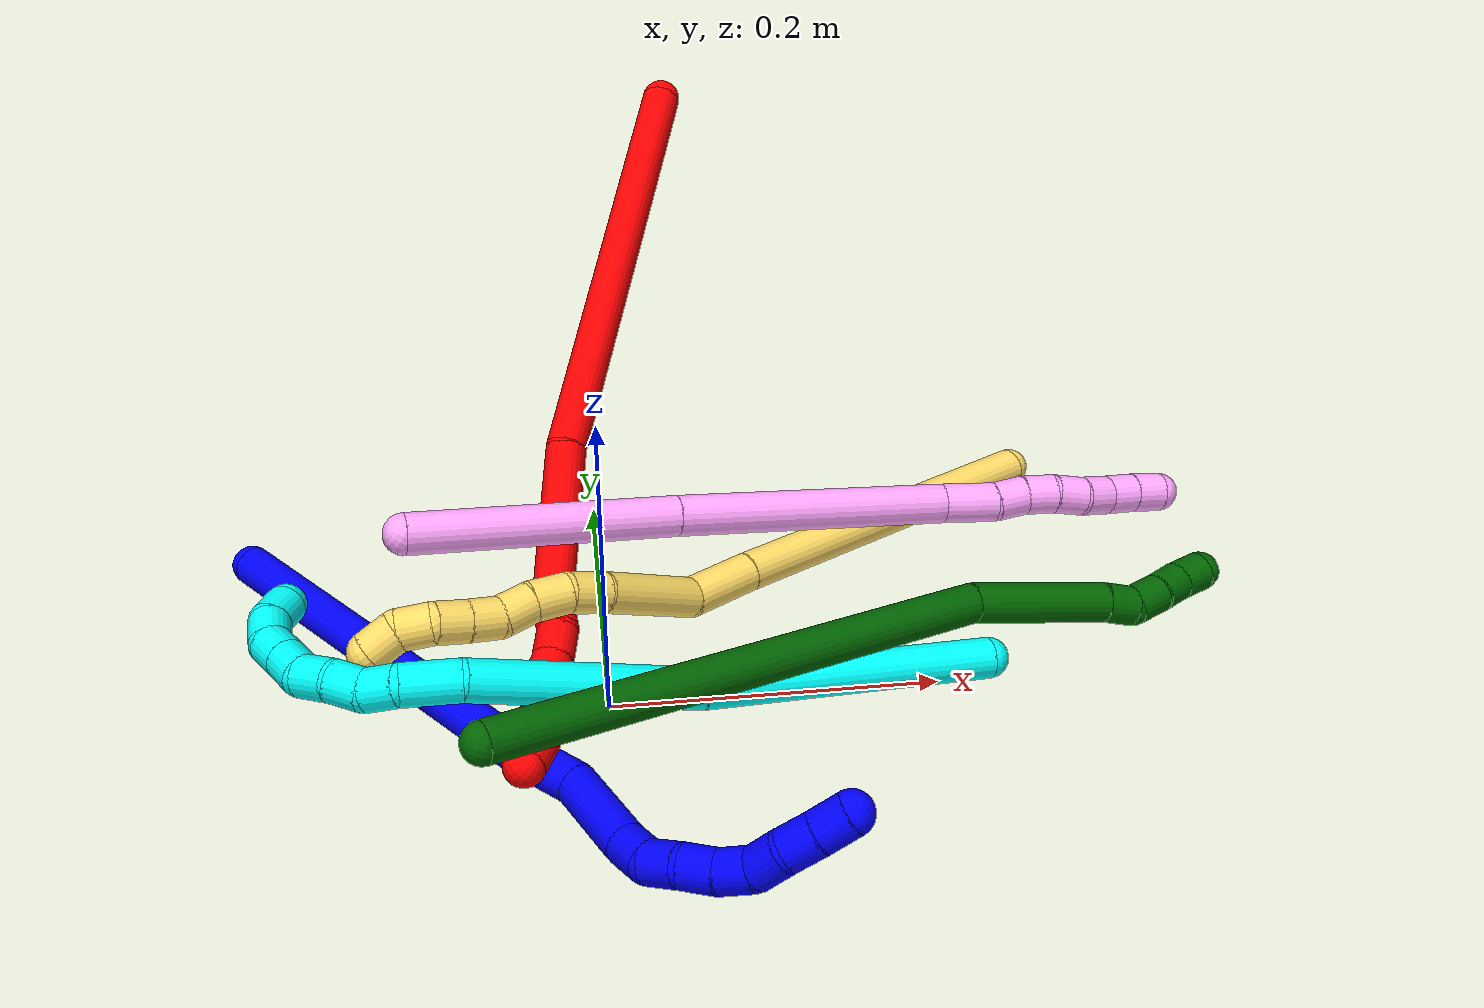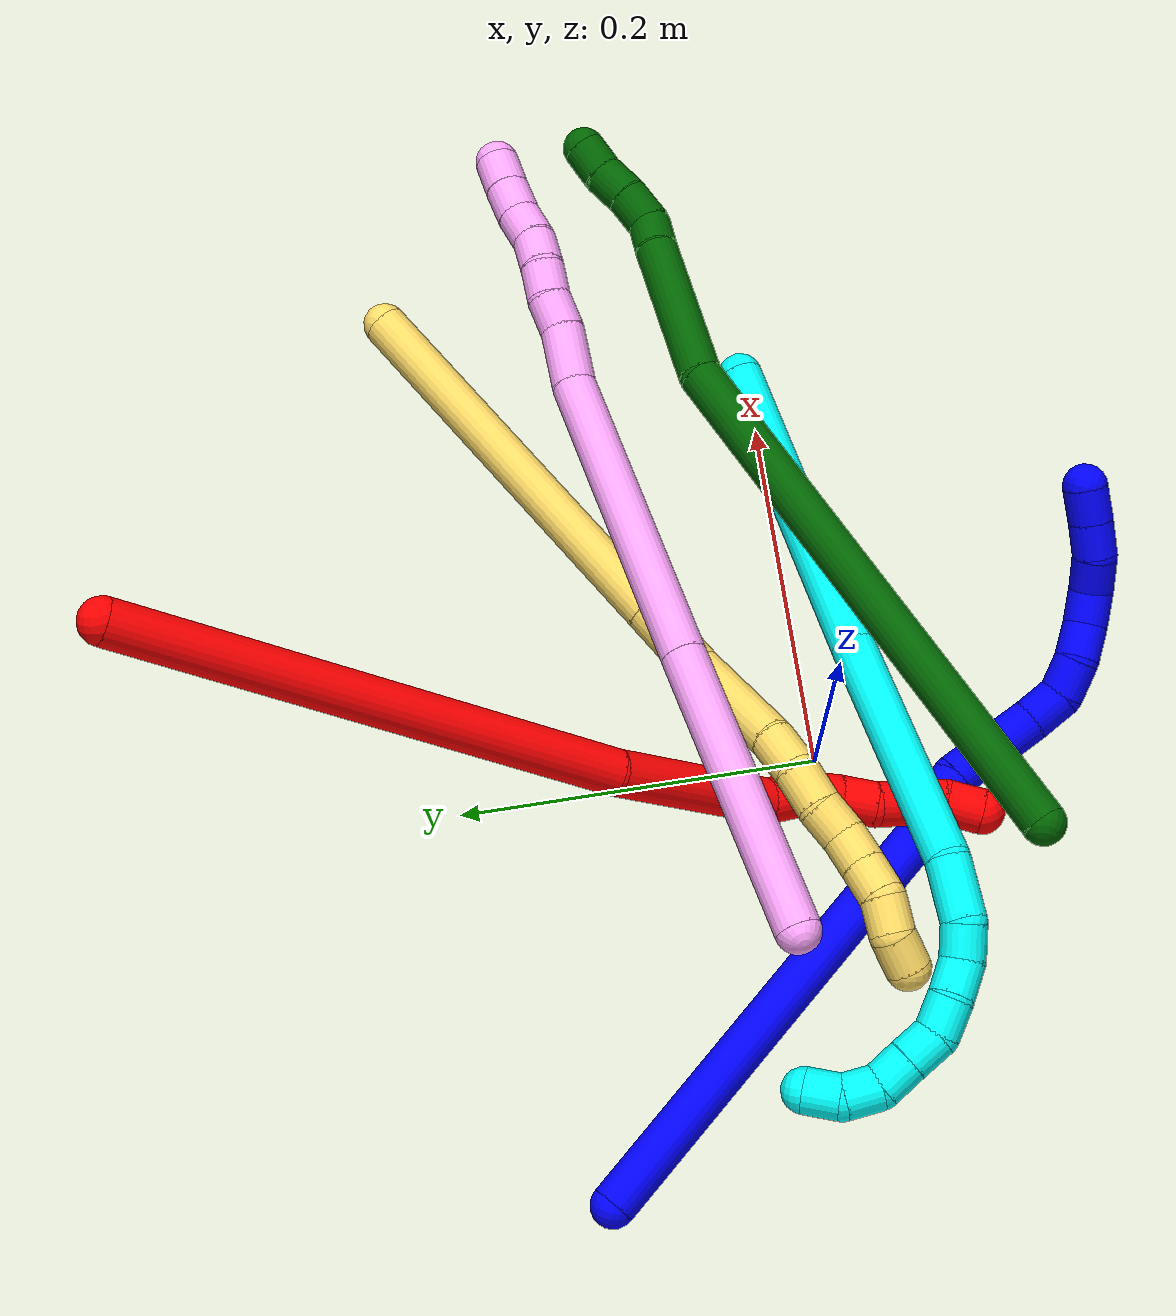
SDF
<sdf version="1.7">
 <world name="default">
  <plugin name="TubeGeneratorPlugin" filename="libtube_generator_plugin.so"/>
  <model name="photoneo_s_sensor">
   <static>1</static>
   <pose>0 0 2 1.57079 1.57079 3.14159</pose>
   <link name="link">
    <inertial><mass>0.1</mass></inertial>
    <sensor name="sensor" type="depth">
     <update_rate>30</update_rate>
     <camera>
      <horizontal_fov>1.22</horizontal_fov>
      <image><width>1920</width><height>1200</height><format>B8G8R8</format></image>
      <clip><near>0.1</near><far>4</far></clip>
      <depth_camera><output>points</output></depth_camera>
     </camera>
     <plugin name="camera_plugin" filename="libgazebo_ros_depth_camera.so">
      <baseline>0.2</baseline>
      <alwaysOn>1</alwaysOn>
      <updateRate>0.0</updateRate>
      <cameraName>camera_ir</cameraName>
      <imageTopicName>/camera/color/image_raw</imageTopicName>
      <cameraInfoTopicName>/camera/color/camera_info</cameraInfoTopicName>
      <depthImageTopicName>/camera/depth/image_raw</depthImageTopicName>
      <depthImageCameraInfoTopicName>/camera/depth/camera_info</depthImageCameraInfoTopicName>
      <pointCloudTopicName>/camera/depth/points</pointCloudTopicName>
      <frameName>fr_optical</frameName>
      <pointCloudCutoff>0.1</pointCloudCutoff>
      <pointCloudCutoffMax>2.0</pointCloudCutoffMax>
      <distortionK1>0</distortionK1>
      <distortionK2>0</distortionK2>
      <distortionK3>0</distortionK3>
      <distortionT1>0</distortionT1>
      <distortionT2>0</distortionT2>
      <CxPrime>0</CxPrime>
      <Cx>0</Cx>
      <Cy>0</Cy>
      <focalLength>0</focalLength>
      <hackBaseline>0</hackBaseline>
     </plugin>
    </sensor>
   </link>
  </model>
  <gravity>0 0 -9.8</gravity>
  <magnetic_field>6e-06 2.3e-05 -4.2e-05</magnetic_field>
  <atmosphere type="adiabatic"/>
  <physics name="default_physics" default="0" type="ode">
   <max_step_size>0.003</max_step_size>
   <real_time_factor>1</real_time_factor>
   <real_time_update_rate>1000</real_time_update_rate>
   <max_contacts>10000</max_contacts>
   <ode>
    <solver>
     <type>quick</type>
     <iters>100</iters>
     <sor>1.3</sor>
     <use_dynamic_moi_rescaling>0</use_dynamic_moi_rescaling>
    </solver>
    <constraints>
     <contact_max_correcting_vel>0</contact_max_correcting_vel>
     <contact_surface_layer>0.001</contact_surface_layer>
     <cfm>0</cfm>
     <erp>0.2</erp>
    </constraints>
   </ode>
  </physics>
  <scene><ambient>0.4 0.4 0.4 1</ambient><background>0.7 0.7 0.7 1</background><shadows>0</shadows></scene>
  <audio><device>default</device></audio>
  <spherical_coordinates>
   <surface_model>EARTH_WGS84</surface_model>
   <latitude_deg>0</latitude_deg>
   <longitude_deg>0</longitude_deg>
   <elevation>0</elevation>
   <heading_deg>0</heading_deg>
  </spherical_coordinates>
  <model name="bin">
   <static>1</static>
   <link name="bottom">
    <collision name="collision-bottom">
     <pose>0 0 -0.01 0 -0 0</pose>
     <geometry><box><size>0.8 0.6 0.02</size></box></geometry>
     <surface>
      <friction><ode><mu>100</mu><mu2>100</mu2></ode></friction>
      <contact><collide_bitmask>65535</collide_bitmask></contact>
     </surface>
    </collision>
   </link>
   <link name="west_wall">
    <collision name="collision-west_wall">
     <pose>-0.41 0 0.1 0 -0 0</pose>
     <geometry><box><size>0.02 0.6 0.2</size></box></geometry>
     <surface>
      <friction><ode><mu>100</mu><mu2>100</mu2></ode></friction>
      <contact><collide_bitmask>65535</collide_bitmask></contact>
     </surface>
    </collision>
   </link>
   <link name="east_wall">
    <collision name="collision-east_wall">
     <pose>0.41 0 0.1 0 -0 0</pose>
     <geometry><box><size>0.02 0.6 0.2</size></box></geometry>
     <surface>
      <friction><ode><mu>100</mu><mu2>100</mu2></ode></friction>
      <contact><collide_bitmask>65535</collide_bitmask></contact>
     </surface>
    </collision>
   </link>
   <link name="south_wall">
    <collision name="collision-south_wall">
     <pose>0 -0.31 0.1 0 -0 0</pose>
     <geometry><box><size>0.8 0.02 0.2</size></box></geometry>
     <surface>
      <friction><ode><mu>100</mu><mu2>100</mu2></ode></friction>
      <contact><collide_bitmask>65535</collide_bitmask></contact>
     </surface>
    </collision>
   </link>
   <link name="north_wall">
    <collision name="collision-north_wall">
     <pose>0 0.31 0.1 0 -0 0</pose>
     <geometry><box><size>0.8 0.02 0.2</size></box></geometry>
     <surface>
      <friction><ode><mu>100</mu><mu2>100</mu2></ode></friction>
      <contact><collide_bitmask>65535</collide_bitmask></contact>
     </surface>
    </collision>
   </link>
  </model>
  <model name="1">
   <static>0</static>
   <link name="1">
    <collision name="collision-cylinder-e_1_1_4">
     <pose>0.082902 -0.089436 0.043331 1.11963 0.695248 0.446577</pose>
     <geometry><cylinder><radius>0.0125</radius><length>0.258836</length></cylinder></geometry>
     <surface>
      <friction><ode><mu>1.16</mu><mu2>1.16</mu2><slip1>0</slip1><slip2>0</slip2></ode></friction>
      <contact><ode><kp>1e+06</kp><kd>1</kd><max_vel>0</max_vel><min_depth>0.001</min_depth></ode></contact>
     </surface>
    </collision>
    <visual name="visual-cylinder-e_1_1_4">
     <pose>0.082902 -0.089436 0.043331 1.11963 0.695248 0.446577</pose>
     <geometry><cylinder><radius>0.0125</radius><length>0.258836</length></cylinder></geometry>
     <material><ambient>0 0 1 1</ambient></material>
    </visual>
    <collision name="collision-cylinder-e_2_4_5">
     <pose>0.179758 -0.193855 0.090988 1.28968 0.729875 0.559598</pose>
     <geometry><cylinder><radius>0.0125</radius><length>0.041855</length></cylinder></geometry>
     <surface>
      <friction><ode><mu>1.16</mu><mu2>1.16</mu2><slip1>0</slip1><slip2>0</slip2></ode></friction>
      <contact><ode><kp>1e+06</kp><kd>1</kd><max_vel>0</max_vel><min_depth>0.001</min_depth></ode></contact>
     </surface>
    </collision>
    <visual name="visual-cylinder-e_2_4_5">
     <pose>0.179758 -0.193855 0.090988 1.28968 0.729875 0.559598</pose>
     <geometry><cylinder><radius>0.0125</radius><length>0.041855</length></cylinder></geometry>
     <material><ambient>0 0 1 1</ambient></material>
    </visual>
    <collision name="collision-cylinder-e_3_5_6">
     <pose>0.208219 -0.22643 0.110018 0.874585 0.564174 0.269324</pose>
     <geometry><cylinder><radius>0.0125</radius><length>0.054259</length></cylinder></geometry>
     <surface>
      <friction><ode><mu>1.16</mu><mu2>1.16</mu2><slip1>0</slip1><slip2>0</slip2></ode></friction>
      <contact><ode><kp>1e+06</kp><kd>1</kd><max_vel>0</max_vel><min_depth>0.001</min_depth></ode></contact>
     </surface>
    </collision>
    <visual name="visual-cylinder-e_3_5_6">
     <pose>0.208219 -0.22643 0.110018 0.874585 0.564174 0.269324</pose>
     <geometry><cylinder><radius>0.0125</radius><length>0.054259</length></cylinder></geometry>
     <material><ambient>0 0 1 1</ambient></material>
    </visual>
    <collision name="collision-cylinder-e_4_6_7">
     <pose>0.230208 -0.249409 0.130704 0.733175 0.748715 0.299432</pose>
     <geometry><cylinder><radius>0.0125</radius><length>0.021985</length></cylinder></geometry>
     <surface>
      <friction><ode><mu>1.16</mu><mu2>1.16</mu2><slip1>0</slip1><slip2>0</slip2></ode></friction>
      <contact><ode><kp>1e+06</kp><kd>1</kd><max_vel>0</max_vel><min_depth>0.001</min_depth></ode></contact>
     </surface>
    </collision>
    <visual name="visual-cylinder-e_4_6_7">
     <pose>0.230208 -0.249409 0.130704 0.733175 0.748715 0.299432</pose>
     <geometry><cylinder><radius>0.0125</radius><length>0.021985</length></cylinder></geometry>
     <material><ambient>0 0 1 1</ambient></material>
    </visual>
    <collision name="collision-cylinder-e_5_7_8">
     <pose>0.247271 -0.259239 0.138203 1.24196 1.1154 0.839416</pose>
     <geometry><cylinder><radius>0.0125</radius><length>0.021334</length></cylinder></geometry>
     <surface>
      <friction><ode><mu>1.16</mu><mu2>1.16</mu2><slip1>0</slip1><slip2>0</slip2></ode></friction>
      <contact><ode><kp>1e+06</kp><kd>1</kd><max_vel>0</max_vel><min_depth>0.001</min_depth></ode></contact>
     </surface>
    </collision>
    <visual name="visual-cylinder-e_5_7_8">
     <pose>0.247271 -0.259239 0.138203 1.24196 1.1154 0.839416</pose>
     <geometry><cylinder><radius>0.0125</radius><length>0.021334</length></cylinder></geometry>
     <material><ambient>0 0 1 1</ambient></material>
    </visual>
    <collision name="collision-cylinder-e_6_8_9">
     <pose>0.265037 -0.26982 0.139038 1.68096 0.924239 1.01522</pose>
     <geometry><cylinder><radius>0.0125</radius><length>0.020512</length></cylinder></geometry>
     <surface>
      <friction><ode><mu>1.16</mu><mu2>1.16</mu2><slip1>0</slip1><slip2>0</slip2></ode></friction>
      <contact><ode><kp>1e+06</kp><kd>1</kd><max_vel>0</max_vel><min_depth>0.001</min_depth></ode></contact>
     </surface>
    </collision>
    <visual name="visual-cylinder-e_6_8_9">
     <pose>0.265037 -0.26982 0.139038 1.68096 0.924239 1.01522</pose>
     <geometry><cylinder><radius>0.0125</radius><length>0.020512</length></cylinder></geometry>
     <material><ambient>0 0 1 1</ambient></material>
    </visual>
    <collision name="collision-cylinder-e_7_9_10">
     <pose>0.282452 -0.2799 0.137291 1.8357 1.15441 1.41057</pose>
     <geometry><cylinder><radius>0.0125</radius><length>0.020184</length></cylinder></geometry>
     <surface>
      <friction><ode><mu>1.16</mu><mu2>1.16</mu2><slip1>0</slip1><slip2>0</slip2></ode></friction>
      <contact><ode><kp>1e+06</kp><kd>1</kd><max_vel>0</max_vel><min_depth>0.001</min_depth></ode></contact>
     </surface>
    </collision>
    <visual name="visual-cylinder-e_7_9_10">
     <pose>0.282452 -0.2799 0.137291 1.8357 1.15441 1.41057</pose>
     <geometry><cylinder><radius>0.0125</radius><length>0.020184</length></cylinder></geometry>
     <material><ambient>0 0 1 1</ambient></material>
    </visual>
    <collision name="collision-cylinder-e_8_10_11">
     <pose>0.302112 -0.283326 0.135245 -2.65716 1.4653 -2.60559</pose>
     <geometry><cylinder><radius>0.0125</radius><length>0.020976</length></cylinder></geometry>
     <surface>
      <friction><ode><mu>1.16</mu><mu2>1.16</mu2><slip1>0</slip1><slip2>0</slip2></ode></friction>
      <contact><ode><kp>1e+06</kp><kd>1</kd><max_vel>0</max_vel><min_depth>0.001</min_depth></ode></contact>
     </surface>
    </collision>
    <visual name="visual-cylinder-e_8_10_11">
     <pose>0.302112 -0.283326 0.135245 -2.65716 1.4653 -2.60559</pose>
     <geometry><cylinder><radius>0.0125</radius><length>0.020976</length></cylinder></geometry>
     <material><ambient>0 0 1 1</ambient></material>
    </visual>
    <collision name="collision-cylinder-e_9_11_12">
     <pose>0.321951 -0.283582 0.130909 2.91607 1.21984 2.82028</pose>
     <geometry><cylinder><radius>0.0125</radius><length>0.020042</length></cylinder></geometry>
     <surface>
      <friction><ode><mu>1.16</mu><mu2>1.16</mu2><slip1>0</slip1><slip2>0</slip2></ode></friction>
      <contact><ode><kp>1e+06</kp><kd>1</kd><max_vel>0</max_vel><min_depth>0.001</min_depth></ode></contact>
     </surface>
    </collision>
    <visual name="visual-cylinder-e_9_11_12">
     <pose>0.321951 -0.283582 0.130909 2.91607 1.21984 2.82028</pose>
     <geometry><cylinder><radius>0.0125</radius><length>0.020042</length></cylinder></geometry>
     <material><ambient>0 0 1 1</ambient></material>
    </visual>
    <collision name="collision-cylinder-e_10_12_2">
     <pose>0.340665 -0.284813 0.12389 3.01624 1.1932 2.9573</pose>
     <geometry><cylinder><radius>0.0125</radius><length>0.020016</length></cylinder></geometry>
     <surface>
      <friction><ode><mu>1.16</mu><mu2>1.16</mu2><slip1>0</slip1><slip2>0</slip2></ode></friction>
      <contact><ode><kp>1e+06</kp><kd>1</kd><max_vel>0</max_vel><min_depth>0.001</min_depth></ode></contact>
     </surface>
    </collision>
    <visual name="visual-cylinder-e_10_12_2">
     <pose>0.340665 -0.284813 0.12389 3.01624 1.1932 2.9573</pose>
     <geometry><cylinder><radius>0.0125</radius><length>0.020016</length></cylinder></geometry>
     <material><ambient>0 0 1 1</ambient></material>
    </visual>
    <collision name="collision-sphere-2">
     <pose>0.349968 -0.285275 0.120229 0 -0 0</pose>
     <geometry><sphere><radius>0.0125</radius></sphere></geometry>
     <surface>
      <friction><ode><mu>1.16</mu><mu2>1.16</mu2><slip1>0</slip1><slip2>0</slip2></ode></friction>
      <contact><ode><kp>1e+06</kp><kd>1</kd><max_vel>0</max_vel><min_depth>0.001</min_depth></ode></contact>
     </surface>
    </collision>
    <visual name="visual-sphere-2">
     <pose>0.349968 -0.285275 0.120229 0 -0 0</pose>
     <geometry><sphere><radius>0.0125</radius></sphere></geometry>
     <material><ambient>0 0 1 1</ambient></material>
    </visual>
    <collision name="collision-sphere-12">
     <pose>0.331362 -0.284352 0.127551 0 -0 0</pose>
     <geometry><sphere><radius>0.0125</radius></sphere></geometry>
     <surface>
      <friction><ode><mu>1.16</mu><mu2>1.16</mu2><slip1>0</slip1><slip2>0</slip2></ode></friction>
      <contact><ode><kp>1e+06</kp><kd>1</kd><max_vel>0</max_vel><min_depth>0.001</min_depth></ode></contact>
     </surface>
    </collision>
    <visual name="visual-sphere-12">
     <pose>0.331362 -0.284352 0.127551 0 -0 0</pose>
     <geometry><sphere><radius>0.0125</radius></sphere></geometry>
     <material><ambient>0 0 1 1</ambient></material>
    </visual>
    <collision name="collision-sphere-11">
     <pose>0.312541 -0.282811 0.134267 0 -0 0</pose>
     <geometry><sphere><radius>0.0125</radius></sphere></geometry>
     <surface>
      <friction><ode><mu>1.16</mu><mu2>1.16</mu2><slip1>0</slip1><slip2>0</slip2></ode></friction>
      <contact><ode><kp>1e+06</kp><kd>1</kd><max_vel>0</max_vel><min_depth>0.001</min_depth></ode></contact>
     </surface>
    </collision>
    <visual name="visual-sphere-11">
     <pose>0.312541 -0.282811 0.134267 0 -0 0</pose>
     <geometry><sphere><radius>0.0125</radius></sphere></geometry>
     <material><ambient>0 0 1 1</ambient></material>
    </visual>
    <collision name="collision-sphere-10">
     <pose>0.291682 -0.28384 0.136222 0 -0 0</pose>
     <geometry><sphere><radius>0.0125</radius></sphere></geometry>
     <surface>
      <friction><ode><mu>1.16</mu><mu2>1.16</mu2><slip1>0</slip1><slip2>0</slip2></ode></friction>
      <contact><ode><kp>1e+06</kp><kd>1</kd><max_vel>0</max_vel><min_depth>0.001</min_depth></ode></contact>
     </surface>
    </collision>
    <visual name="visual-sphere-10">
     <pose>0.291682 -0.28384 0.136222 0 -0 0</pose>
     <geometry><sphere><radius>0.0125</radius></sphere></geometry>
     <material><ambient>0 0 1 1</ambient></material>
    </visual>
    <collision name="collision-sphere-9">
     <pose>0.273222 -0.275961 0.138359 0 -0 0</pose>
     <geometry><sphere><radius>0.0125</radius></sphere></geometry>
     <surface>
      <friction><ode><mu>1.16</mu><mu2>1.16</mu2><slip1>0</slip1><slip2>0</slip2></ode></friction>
      <contact><ode><kp>1e+06</kp><kd>1</kd><max_vel>0</max_vel><min_depth>0.001</min_depth></ode></contact>
     </surface>
    </collision>
    <visual name="visual-sphere-9">
     <pose>0.273222 -0.275961 0.138359 0 -0 0</pose>
     <geometry><sphere><radius>0.0125</radius></sphere></geometry>
     <material><ambient>0 0 1 1</ambient></material>
    </visual>
    <collision name="collision-sphere-4">
     <pose>0.165804 -0.178871 0.086661 0 -0 0</pose>
     <geometry><sphere><radius>0.0125</radius></sphere></geometry>
     <surface>
      <friction><ode><mu>1.16</mu><mu2>1.16</mu2><slip1>0</slip1><slip2>0</slip2></ode></friction>
      <contact><ode><kp>1e+06</kp><kd>1</kd><max_vel>0</max_vel><min_depth>0.001</min_depth></ode></contact>
     </surface>
    </collision>
    <visual name="visual-sphere-4">
     <pose>0.165804 -0.178871 0.086661 0 -0 0</pose>
     <geometry><sphere><radius>0.0125</radius></sphere></geometry>
     <material><ambient>0 0 1 1</ambient></material>
    </visual>
    <collision name="collision-sphere-1">
     <geometry><sphere><radius>0.0125</radius></sphere></geometry>
     <surface>
      <friction><ode><mu>1.16</mu><mu2>1.16</mu2><slip1>0</slip1><slip2>0</slip2></ode></friction>
      <contact><ode><kp>1e+06</kp><kd>1</kd><max_vel>0</max_vel><min_depth>0.001</min_depth></ode></contact>
     </surface>
    </collision>
    <visual name="visual-sphere-1">
     <geometry><sphere><radius>0.0125</radius></sphere></geometry>
     <material><ambient>0 0 1 1</ambient></material>
    </visual>
    <collision name="collision-sphere-8">
     <pose>0.256851 -0.263679 0.139718 0 -0 0</pose>
     <geometry><sphere><radius>0.0125</radius></sphere></geometry>
     <surface>
      <friction><ode><mu>1.16</mu><mu2>1.16</mu2><slip1>0</slip1><slip2>0</slip2></ode></friction>
      <contact><ode><kp>1e+06</kp><kd>1</kd><max_vel>0</max_vel><min_depth>0.001</min_depth></ode></contact>
     </surface>
    </collision>
    <visual name="visual-sphere-8">
     <pose>0.256851 -0.263679 0.139718 0 -0 0</pose>
     <geometry><sphere><radius>0.0125</radius></sphere></geometry>
     <material><ambient>0 0 1 1</ambient></material>
    </visual>
    <collision name="collision-sphere-5">
     <pose>0.193712 -0.20884 0.095315 0 -0 0</pose>
     <geometry><sphere><radius>0.0125</radius></sphere></geometry>
     <surface>
      <friction><ode><mu>1.16</mu><mu2>1.16</mu2><slip1>0</slip1><slip2>0</slip2></ode></friction>
      <contact><ode><kp>1e+06</kp><kd>1</kd><max_vel>0</max_vel><min_depth>0.001</min_depth></ode></contact>
     </surface>
    </collision>
    <visual name="visual-sphere-5">
     <pose>0.193712 -0.20884 0.095315 0 -0 0</pose>
     <geometry><sphere><radius>0.0125</radius></sphere></geometry>
     <material><ambient>0 0 1 1</ambient></material>
    </visual>
    <collision name="collision-sphere-6">
     <pose>0.222726 -0.24402 0.12472 0 -0 0</pose>
     <geometry><sphere><radius>0.0125</radius></sphere></geometry>
     <surface>
      <friction><ode><mu>1.16</mu><mu2>1.16</mu2><slip1>0</slip1><slip2>0</slip2></ode></friction>
      <contact><ode><kp>1e+06</kp><kd>1</kd><max_vel>0</max_vel><min_depth>0.001</min_depth></ode></contact>
     </surface>
    </collision>
    <visual name="visual-sphere-6">
     <pose>0.222726 -0.24402 0.12472 0 -0 0</pose>
     <geometry><sphere><radius>0.0125</radius></sphere></geometry>
     <material><ambient>0 0 1 1</ambient></material>
    </visual>
    <collision name="collision-sphere-7">
     <pose>0.237691 -0.254798 0.136688 0 -0 0</pose>
     <geometry><sphere><radius>0.0125</radius></sphere></geometry>
     <surface>
      <friction><ode><mu>1.16</mu><mu2>1.16</mu2><slip1>0</slip1><slip2>0</slip2></ode></friction>
      <contact><ode><kp>1e+06</kp><kd>1</kd><max_vel>0</max_vel><min_depth>0.001</min_depth></ode></contact>
     </surface>
    </collision>
    <visual name="visual-sphere-7">
     <pose>0.237691 -0.254798 0.136688 0 -0 0</pose>
     <geometry><sphere><radius>0.0125</radius></sphere></geometry>
     <material><ambient>0 0 1 1</ambient></material>
    </visual>
    <inertial>
     <pose>0.162724 -0.166149 0.080758 0 -0 0</pose>
     <mass>0.5</mass>
     <inertia>
      <ixx>0.001545</ixx>
      <ixy>0</ixy>
      <ixz>0</ixz>
      <iyy>0.001429</iyy>
      <iyz>0</iyz>
      <izz>7.9e-05</izz>
     </inertia>
    </inertial>
   </link>
   <pose>-0.224857 0.148812 0.011493 1.32074 -0.745249 -0.333215</pose>
  </model>
  <model name="2">
   <static>0</static>
   <link name="2">
    <collision name="collision-cylinder-e_1_1_4">
     <pose>-0.050486 -0.10319 -0.079267 2.22582 -0.370117 -0.726042</pose>
     <geometry><cylinder><radius>0.0125</radius><length>0.279143</length></cylinder></geometry>
     <surface>
      <friction><ode><mu>1.16</mu><mu2>1.16</mu2><slip1>0</slip1><slip2>0</slip2></ode></friction>
      <contact><ode><kp>1e+06</kp><kd>1</kd><max_vel>0</max_vel><min_depth>0.001</min_depth></ode></contact>
     </surface>
    </collision>
    <visual name="visual-cylinder-e_1_1_4">
     <pose>-0.050486 -0.10319 -0.079267 2.22582 -0.370117 -0.726042</pose>
     <geometry><cylinder><radius>0.0125</radius><length>0.279143</length></cylinder></geometry>
     <material><ambient>1 0 0 1</ambient></material>
    </visual>
    <collision name="collision-cylinder-e_2_4_5">
     <pose>-0.109868 -0.246645 -0.185816 2.16632 -0.180881 -0.338715</pose>
     <geometry><cylinder><radius>0.0125</radius><length>0.098889</length></cylinder></geometry>
     <surface>
      <friction><ode><mu>1.16</mu><mu2>1.16</mu2><slip1>0</slip1><slip2>0</slip2></ode></friction>
      <contact><ode><kp>1e+06</kp><kd>1</kd><max_vel>0</max_vel><min_depth>0.001</min_depth></ode></contact>
     </surface>
    </collision>
    <visual name="visual-cylinder-e_2_4_5">
     <pose>-0.109868 -0.246645 -0.185816 2.16632 -0.180881 -0.338715</pose>
     <geometry><cylinder><radius>0.0125</radius><length>0.098889</length></cylinder></geometry>
     <material><ambient>1 0 0 1</ambient></material>
    </visual>
    <collision name="collision-cylinder-e_3_5_6">
     <pose>-0.122179 -0.296604 -0.214586 1.72296 -0.335178 -0.389202</pose>
     <geometry><cylinder><radius>0.0125</radius><length>0.02077</length></cylinder></geometry>
     <surface>
      <friction><ode><mu>1.16</mu><mu2>1.16</mu2><slip1>0</slip1><slip2>0</slip2></ode></friction>
      <contact><ode><kp>1e+06</kp><kd>1</kd><max_vel>0</max_vel><min_depth>0.001</min_depth></ode></contact>
     </surface>
    </collision>
    <visual name="visual-cylinder-e_3_5_6">
     <pose>-0.122179 -0.296604 -0.214586 1.72296 -0.335178 -0.389202</pose>
     <geometry><cylinder><radius>0.0125</radius><length>0.02077</length></cylinder></geometry>
     <material><ambient>1 0 0 1</ambient></material>
    </visual>
    <collision name="collision-cylinder-e_4_6_7">
     <pose>-0.130624 -0.314691 -0.22006 2.01431 -0.49603 -0.762143</pose>
     <geometry><cylinder><radius>0.0125</radius><length>0.021134</length></cylinder></geometry>
     <surface>
      <friction><ode><mu>1.16</mu><mu2>1.16</mu2><slip1>0</slip1><slip2>0</slip2></ode></friction>
      <contact><ode><kp>1e+06</kp><kd>1</kd><max_vel>0</max_vel><min_depth>0.001</min_depth></ode></contact>
     </surface>
    </collision>
    <visual name="visual-cylinder-e_4_6_7">
     <pose>-0.130624 -0.314691 -0.22006 2.01431 -0.49603 -0.762143</pose>
     <geometry><cylinder><radius>0.0125</radius><length>0.021134</length></cylinder></geometry>
     <material><ambient>1 0 0 1</ambient></material>
    </visual>
    <collision name="collision-cylinder-e_5_7_8">
     <pose>-0.142248 -0.329816 -0.22746 2.03998 -0.718267 -1.09724</pose>
     <geometry><cylinder><radius>0.0125</radius><length>0.020044</length></cylinder></geometry>
     <surface>
      <friction><ode><mu>1.16</mu><mu2>1.16</mu2><slip1>0</slip1><slip2>0</slip2></ode></friction>
      <contact><ode><kp>1e+06</kp><kd>1</kd><max_vel>0</max_vel><min_depth>0.001</min_depth></ode></contact>
     </surface>
    </collision>
    <visual name="visual-cylinder-e_5_7_8">
     <pose>-0.142248 -0.329816 -0.22746 2.03998 -0.718267 -1.09724</pose>
     <geometry><cylinder><radius>0.0125</radius><length>0.020044</length></cylinder></geometry>
     <material><ambient>1 0 0 1</ambient></material>
    </visual>
    <collision name="collision-cylinder-e_6_8_9">
     <pose>-0.152746 -0.345369 -0.23351 1.86127 -0.400814 -0.532524</pose>
     <geometry><cylinder><radius>0.0125</radius><length>0.020001</length></cylinder></geometry>
     <surface>
      <friction><ode><mu>1.16</mu><mu2>1.16</mu2><slip1>0</slip1><slip2>0</slip2></ode></friction>
      <contact><ode><kp>1e+06</kp><kd>1</kd><max_vel>0</max_vel><min_depth>0.001</min_depth></ode></contact>
     </surface>
    </collision>
    <visual name="visual-cylinder-e_6_8_9">
     <pose>-0.152746 -0.345369 -0.23351 1.86127 -0.400814 -0.532524</pose>
     <geometry><cylinder><radius>0.0125</radius><length>0.020001</length></cylinder></geometry>
     <material><ambient>1 0 0 1</ambient></material>
    </visual>
    <collision name="collision-cylinder-e_7_9_10">
     <pose>-0.162995 -0.361774 -0.237665 1.76841 -0.687323 -0.823339</pose>
     <geometry><cylinder><radius>0.0125</radius><length>0.020009</length></cylinder></geometry>
     <surface>
      <friction><ode><mu>1.16</mu><mu2>1.16</mu2><slip1>0</slip1><slip2>0</slip2></ode></friction>
      <contact><ode><kp>1e+06</kp><kd>1</kd><max_vel>0</max_vel><min_depth>0.001</min_depth></ode></contact>
     </surface>
    </collision>
    <visual name="visual-cylinder-e_7_9_10">
     <pose>-0.162995 -0.361774 -0.237665 1.76841 -0.687323 -0.823339</pose>
     <geometry><cylinder><radius>0.0125</radius><length>0.020009</length></cylinder></geometry>
     <material><ambient>1 0 0 1</ambient></material>
    </visual>
    <collision name="collision-cylinder-e_8_10_2">
     <pose>-0.176718 -0.375204 -0.242576 2.09656 -0.828799 -1.30453</pose>
     <geometry><cylinder><radius>0.0125</radius><length>0.02001</length></cylinder></geometry>
     <surface>
      <friction><ode><mu>1.16</mu><mu2>1.16</mu2><slip1>0</slip1><slip2>0</slip2></ode></friction>
      <contact><ode><kp>1e+06</kp><kd>1</kd><max_vel>0</max_vel><min_depth>0.001</min_depth></ode></contact>
     </surface>
    </collision>
    <visual name="visual-cylinder-e_8_10_2">
     <pose>-0.176718 -0.375204 -0.242576 2.09656 -0.828799 -1.30453</pose>
     <geometry><cylinder><radius>0.0125</radius><length>0.02001</length></cylinder></geometry>
     <material><ambient>1 0 0 1</ambient></material>
    </visual>
    <collision name="collision-sphere-2">
     <pose>-0.184092 -0.381052 -0.245969 0 -0 0</pose>
     <geometry><sphere><radius>0.0125</radius></sphere></geometry>
     <surface>
      <friction><ode><mu>1.16</mu><mu2>1.16</mu2><slip1>0</slip1><slip2>0</slip2></ode></friction>
      <contact><ode><kp>1e+06</kp><kd>1</kd><max_vel>0</max_vel><min_depth>0.001</min_depth></ode></contact>
     </surface>
    </collision>
    <visual name="visual-sphere-2">
     <pose>-0.184092 -0.381052 -0.245969 0 -0 0</pose>
     <geometry><sphere><radius>0.0125</radius></sphere></geometry>
     <material><ambient>1 0 0 1</ambient></material>
    </visual>
    <collision name="collision-sphere-10">
     <pose>-0.169343 -0.369356 -0.239183 0 -0 0</pose>
     <geometry><sphere><radius>0.0125</radius></sphere></geometry>
     <surface>
      <friction><ode><mu>1.16</mu><mu2>1.16</mu2><slip1>0</slip1><slip2>0</slip2></ode></friction>
      <contact><ode><kp>1e+06</kp><kd>1</kd><max_vel>0</max_vel><min_depth>0.001</min_depth></ode></contact>
     </surface>
    </collision>
    <visual name="visual-sphere-10">
     <pose>-0.169343 -0.369356 -0.239183 0 -0 0</pose>
     <geometry><sphere><radius>0.0125</radius></sphere></geometry>
     <material><ambient>1 0 0 1</ambient></material>
    </visual>
    <collision name="collision-sphere-9">
     <pose>-0.156647 -0.354191 -0.236147 0 -0 0</pose>
     <geometry><sphere><radius>0.0125</radius></sphere></geometry>
     <surface>
      <friction><ode><mu>1.16</mu><mu2>1.16</mu2><slip1>0</slip1><slip2>0</slip2></ode></friction>
      <contact><ode><kp>1e+06</kp><kd>1</kd><max_vel>0</max_vel><min_depth>0.001</min_depth></ode></contact>
     </surface>
    </collision>
    <visual name="visual-sphere-9">
     <pose>-0.156647 -0.354191 -0.236147 0 -0 0</pose>
     <geometry><sphere><radius>0.0125</radius></sphere></geometry>
     <material><ambient>1 0 0 1</ambient></material>
    </visual>
    <collision name="collision-sphere-4">
     <pose>-0.100973 -0.20638 -0.158533 0 -0 0</pose>
     <geometry><sphere><radius>0.0125</radius></sphere></geometry>
     <surface>
      <friction><ode><mu>1.16</mu><mu2>1.16</mu2><slip1>0</slip1><slip2>0</slip2></ode></friction>
      <contact><ode><kp>1e+06</kp><kd>1</kd><max_vel>0</max_vel><min_depth>0.001</min_depth></ode></contact>
     </surface>
    </collision>
    <visual name="visual-sphere-4">
     <pose>-0.100973 -0.20638 -0.158533 0 -0 0</pose>
     <geometry><sphere><radius>0.0125</radius></sphere></geometry>
     <material><ambient>1 0 0 1</ambient></material>
    </visual>
    <collision name="collision-sphere-1">
     <geometry><sphere><radius>0.0125</radius></sphere></geometry>
     <surface>
      <friction><ode><mu>1.16</mu><mu2>1.16</mu2><slip1>0</slip1><slip2>0</slip2></ode></friction>
      <contact><ode><kp>1e+06</kp><kd>1</kd><max_vel>0</max_vel><min_depth>0.001</min_depth></ode></contact>
     </surface>
    </collision>
    <visual name="visual-sphere-1">
     <geometry><sphere><radius>0.0125</radius></sphere></geometry>
     <material><ambient>1 0 0 1</ambient></material>
    </visual>
    <collision name="collision-sphere-8">
     <pose>-0.148844 -0.336547 -0.230872 0 -0 0</pose>
     <geometry><sphere><radius>0.0125</radius></sphere></geometry>
     <surface>
      <friction><ode><mu>1.16</mu><mu2>1.16</mu2><slip1>0</slip1><slip2>0</slip2></ode></friction>
      <contact><ode><kp>1e+06</kp><kd>1</kd><max_vel>0</max_vel><min_depth>0.001</min_depth></ode></contact>
     </surface>
    </collision>
    <visual name="visual-sphere-8">
     <pose>-0.148844 -0.336547 -0.230872 0 -0 0</pose>
     <geometry><sphere><radius>0.0125</radius></sphere></geometry>
     <material><ambient>1 0 0 1</ambient></material>
    </visual>
    <collision name="collision-sphere-5">
     <pose>-0.118763 -0.28691 -0.2131 0 -0 0</pose>
     <geometry><sphere><radius>0.0125</radius></sphere></geometry>
     <surface>
      <friction><ode><mu>1.16</mu><mu2>1.16</mu2><slip1>0</slip1><slip2>0</slip2></ode></friction>
      <contact><ode><kp>1e+06</kp><kd>1</kd><max_vel>0</max_vel><min_depth>0.001</min_depth></ode></contact>
     </surface>
    </collision>
    <visual name="visual-sphere-5">
     <pose>-0.118763 -0.28691 -0.2131 0 -0 0</pose>
     <geometry><sphere><radius>0.0125</radius></sphere></geometry>
     <material><ambient>1 0 0 1</ambient></material>
    </visual>
    <collision name="collision-sphere-6">
     <pose>-0.125595 -0.306297 -0.216072 0 -0 0</pose>
     <geometry><sphere><radius>0.0125</radius></sphere></geometry>
     <surface>
      <friction><ode><mu>1.16</mu><mu2>1.16</mu2><slip1>0</slip1><slip2>0</slip2></ode></friction>
      <contact><ode><kp>1e+06</kp><kd>1</kd><max_vel>0</max_vel><min_depth>0.001</min_depth></ode></contact>
     </surface>
    </collision>
    <visual name="visual-sphere-6">
     <pose>-0.125595 -0.306297 -0.216072 0 -0 0</pose>
     <geometry><sphere><radius>0.0125</radius></sphere></geometry>
     <material><ambient>1 0 0 1</ambient></material>
    </visual>
    <collision name="collision-sphere-7">
     <pose>-0.135653 -0.323086 -0.224048 0 -0 0</pose>
     <geometry><sphere><radius>0.0125</radius></sphere></geometry>
     <surface>
      <friction><ode><mu>1.16</mu><mu2>1.16</mu2><slip1>0</slip1><slip2>0</slip2></ode></friction>
      <contact><ode><kp>1e+06</kp><kd>1</kd><max_vel>0</max_vel><min_depth>0.001</min_depth></ode></contact>
     </surface>
    </collision>
    <visual name="visual-sphere-7">
     <pose>-0.135653 -0.323086 -0.224048 0 -0 0</pose>
     <geometry><sphere><radius>0.0125</radius></sphere></geometry>
     <material><ambient>1 0 0 1</ambient></material>
    </visual>
    <inertial>
     <pose>-0.085919 -0.188543 -0.136897 0 -0 0</pose>
     <mass>0.5</mass>
     <inertia>
      <ixx>0.000179</ixx>
      <ixy>0</ixy>
      <ixz>0</ixz>
      <iyy>-0.001713</iyy>
      <iyz>0</iyz>
      <izz>0.002084</izz>
     </inertia>
    </inertial>
   </link>
   <pose>0.063946 0.348962 0.239665 0.483252 0.647339 0.787085</pose>
  </model>
  <model name="3">
   <static>0</static>
   <link name="3">
    <collision name="collision-cylinder-e_1_1_4">
     <pose>-0.075205 0.017355 -0.047819 -2.79344 -0.976062 2.50182</pose>
     <geometry><cylinder><radius>0.0125</radius><length>0.181588</length></cylinder></geometry>
     <surface>
      <friction><ode><mu>1.16</mu><mu2>1.16</mu2><slip1>0</slip1><slip2>0</slip2></ode></friction>
      <contact><ode><kp>1e+06</kp><kd>1</kd><max_vel>0</max_vel><min_depth>0.001</min_depth></ode></contact>
     </surface>
    </collision>
    <visual name="visual-cylinder-e_1_1_4">
     <pose>-0.075205 0.017355 -0.047819 -2.79344 -0.976062 2.50182</pose>
     <geometry><cylinder><radius>0.0125</radius><length>0.181588</length></cylinder></geometry>
     <material><ambient>0.003922 1 0.996078 1</ambient></material>
    </visual>
    <collision name="collision-cylinder-e_2_4_5">
     <pose>-0.209282 0.036632 -0.135302 -3.09317 -0.977389 3.05057</pose>
     <geometry><cylinder><radius>0.0125</radius><length>0.142028</length></cylinder></geometry>
     <surface>
      <friction><ode><mu>1.16</mu><mu2>1.16</mu2><slip1>0</slip1><slip2>0</slip2></ode></friction>
      <contact><ode><kp>1e+06</kp><kd>1</kd><max_vel>0</max_vel><min_depth>0.001</min_depth></ode></contact>
     </surface>
    </collision>
    <visual name="visual-cylinder-e_2_4_5">
     <pose>-0.209282 0.036632 -0.135302 -3.09317 -0.977389 3.05057</pose>
     <geometry><cylinder><radius>0.0125</radius><length>0.142028</length></cylinder></geometry>
     <material><ambient>0.003922 1 0.996078 1</ambient></material>
    </visual>
    <collision name="collision-cylinder-e_3_5_6">
     <pose>-0.2835 0.042605 -0.181915 -2.61389 -1.08796 2.30149</pose>
     <geometry><cylinder><radius>0.0125</radius><length>0.03465</length></cylinder></geometry>
     <surface>
      <friction><ode><mu>1.16</mu><mu2>1.16</mu2><slip1>0</slip1><slip2>0</slip2></ode></friction>
      <contact><ode><kp>1e+06</kp><kd>1</kd><max_vel>0</max_vel><min_depth>0.001</min_depth></ode></contact>
     </surface>
    </collision>
    <visual name="visual-cylinder-e_3_5_6">
     <pose>-0.2835 0.042605 -0.181915 -2.61389 -1.08796 2.30149</pose>
     <geometry><cylinder><radius>0.0125</radius><length>0.03465</length></cylinder></geometry>
     <material><ambient>0.003922 1 0.996078 1</ambient></material>
    </visual>
    <collision name="collision-cylinder-e_4_6_7">
     <pose>-0.307837 0.051116 -0.189478 -1.70754 -1.10658 1.23275</pose>
     <geometry><cylinder><radius>0.0125</radius><length>0.020114</length></cylinder></geometry>
     <surface>
      <friction><ode><mu>1.16</mu><mu2>1.16</mu2><slip1>0</slip1><slip2>0</slip2></ode></friction>
      <contact><ode><kp>1e+06</kp><kd>1</kd><max_vel>0</max_vel><min_depth>0.001</min_depth></ode></contact>
     </surface>
    </collision>
    <visual name="visual-cylinder-e_4_6_7">
     <pose>-0.307837 0.051116 -0.189478 -1.70754 -1.10658 1.23275</pose>
     <geometry><cylinder><radius>0.0125</radius><length>0.020114</length></cylinder></geometry>
     <material><ambient>0.003922 1 0.996078 1</ambient></material>
    </visual>
    <collision name="collision-cylinder-e_5_7_8">
     <pose>-0.326971 0.056483 -0.189037 -0.70952 -1.43457 0.625058</pose>
     <geometry><cylinder><radius>0.0125</radius><length>0.020473</length></cylinder></geometry>
     <surface>
      <friction><ode><mu>1.16</mu><mu2>1.16</mu2><slip1>0</slip1><slip2>0</slip2></ode></friction>
      <contact><ode><kp>1e+06</kp><kd>1</kd><max_vel>0</max_vel><min_depth>0.001</min_depth></ode></contact>
     </surface>
    </collision>
    <visual name="visual-cylinder-e_5_7_8">
     <pose>-0.326971 0.056483 -0.189037 -0.70952 -1.43457 0.625058</pose>
     <geometry><cylinder><radius>0.0125</radius><length>0.020473</length></cylinder></geometry>
     <material><ambient>0.003922 1 0.996078 1</ambient></material>
    </visual>
    <collision name="collision-cylinder-e_6_8_9">
     <pose>-0.346859 0.060234 -0.18555 -0.863556 -1.20407 0.61325</pose>
     <geometry><cylinder><radius>0.0125</radius><length>0.020881</length></cylinder></geometry>
     <surface>
      <friction><ode><mu>1.16</mu><mu2>1.16</mu2><slip1>0</slip1><slip2>0</slip2></ode></friction>
      <contact><ode><kp>1e+06</kp><kd>1</kd><max_vel>0</max_vel><min_depth>0.001</min_depth></ode></contact>
     </surface>
    </collision>
    <visual name="visual-cylinder-e_6_8_9">
     <pose>-0.346859 0.060234 -0.18555 -0.863556 -1.20407 0.61325</pose>
     <geometry><cylinder><radius>0.0125</radius><length>0.020881</length></cylinder></geometry>
     <material><ambient>0.003922 1 0.996078 1</ambient></material>
    </visual>
    <collision name="collision-cylinder-e_7_9_10">
     <pose>-0.364674 0.063095 -0.177113 -0.002479 -0.930954 0.001245</pose>
     <geometry><cylinder><radius>0.0125</radius><length>0.020116</length></cylinder></geometry>
     <surface>
      <friction><ode><mu>1.16</mu><mu2>1.16</mu2><slip1>0</slip1><slip2>0</slip2></ode></friction>
      <contact><ode><kp>1e+06</kp><kd>1</kd><max_vel>0</max_vel><min_depth>0.001</min_depth></ode></contact>
     </surface>
    </collision>
    <visual name="visual-cylinder-e_7_9_10">
     <pose>-0.364674 0.063095 -0.177113 -0.002479 -0.930954 0.001245</pose>
     <geometry><cylinder><radius>0.0125</radius><length>0.020116</length></cylinder></geometry>
     <material><ambient>0.003922 1 0.996078 1</ambient></material>
    </visual>
    <collision name="collision-cylinder-e_8_10_11">
     <pose>-0.380914 0.063225 -0.16532 -0.019982 -0.954502 0.010333</pose>
     <geometry><cylinder><radius>0.0125</radius><length>0.020027</length></cylinder></geometry>
     <surface>
      <friction><ode><mu>1.16</mu><mu2>1.16</mu2><slip1>0</slip1><slip2>0</slip2></ode></friction>
      <contact><ode><kp>1e+06</kp><kd>1</kd><max_vel>0</max_vel><min_depth>0.001</min_depth></ode></contact>
     </surface>
    </collision>
    <visual name="visual-cylinder-e_8_10_11">
     <pose>-0.380914 0.063225 -0.16532 -0.019982 -0.954502 0.010333</pose>
     <geometry><cylinder><radius>0.0125</radius><length>0.020027</length></cylinder></geometry>
     <material><ambient>0.003922 1 0.996078 1</ambient></material>
    </visual>
    <collision name="collision-cylinder-e_9_11_12">
     <pose>-0.394178 0.061035 -0.151219 0.270492 -0.533205 -0.074292</pose>
     <geometry><cylinder><radius>0.0125</radius><length>0.020038</length></cylinder></geometry>
     <surface>
      <friction><ode><mu>1.16</mu><mu2>1.16</mu2><slip1>0</slip1><slip2>0</slip2></ode></friction>
      <contact><ode><kp>1e+06</kp><kd>1</kd><max_vel>0</max_vel><min_depth>0.001</min_depth></ode></contact>
     </surface>
    </collision>
    <visual name="visual-cylinder-e_9_11_12">
     <pose>-0.394178 0.061035 -0.151219 0.270492 -0.533205 -0.074292</pose>
     <geometry><cylinder><radius>0.0125</radius><length>0.020038</length></cylinder></geometry>
     <material><ambient>0.003922 1 0.996078 1</ambient></material>
    </visual>
    <collision name="collision-cylinder-e_10_12_2">
     <pose>-0.399594 0.056822 -0.13305 0.191222 -0.032168 -0.003085</pose>
     <geometry><cylinder><radius>0.0125</radius><length>0.020084</length></cylinder></geometry>
     <surface>
      <friction><ode><mu>1.16</mu><mu2>1.16</mu2><slip1>0</slip1><slip2>0</slip2></ode></friction>
      <contact><ode><kp>1e+06</kp><kd>1</kd><max_vel>0</max_vel><min_depth>0.001</min_depth></ode></contact>
     </surface>
    </collision>
    <visual name="visual-cylinder-e_10_12_2">
     <pose>-0.399594 0.056822 -0.13305 0.191222 -0.032168 -0.003085</pose>
     <geometry><cylinder><radius>0.0125</radius><length>0.020084</length></cylinder></geometry>
     <material><ambient>0.003922 1 0.996078 1</ambient></material>
    </visual>
    <collision name="collision-sphere-2">
     <pose>-0.399917 0.054914 -0.123196 0 -0 0</pose>
     <geometry><sphere><radius>0.0125</radius></sphere></geometry>
     <surface>
      <friction><ode><mu>1.16</mu><mu2>1.16</mu2><slip1>0</slip1><slip2>0</slip2></ode></friction>
      <contact><ode><kp>1e+06</kp><kd>1</kd><max_vel>0</max_vel><min_depth>0.001</min_depth></ode></contact>
     </surface>
    </collision>
    <visual name="visual-sphere-2">
     <pose>-0.399917 0.054914 -0.123196 0 -0 0</pose>
     <geometry><sphere><radius>0.0125</radius></sphere></geometry>
     <material><ambient>0.003922 1 0.996078 1</ambient></material>
    </visual>
    <collision name="collision-sphere-12">
     <pose>-0.399271 0.05873 -0.142904 0 -0 0</pose>
     <geometry><sphere><radius>0.0125</radius></sphere></geometry>
     <surface>
      <friction><ode><mu>1.16</mu><mu2>1.16</mu2><slip1>0</slip1><slip2>0</slip2></ode></friction>
      <contact><ode><kp>1e+06</kp><kd>1</kd><max_vel>0</max_vel><min_depth>0.001</min_depth></ode></contact>
     </surface>
    </collision>
    <visual name="visual-sphere-12">
     <pose>-0.399271 0.05873 -0.142904 0 -0 0</pose>
     <geometry><sphere><radius>0.0125</radius></sphere></geometry>
     <material><ambient>0.003922 1 0.996078 1</ambient></material>
    </visual>
    <collision name="collision-sphere-11">
     <pose>-0.389085 0.063341 -0.159534 0 -0 0</pose>
     <geometry><sphere><radius>0.0125</radius></sphere></geometry>
     <surface>
      <friction><ode><mu>1.16</mu><mu2>1.16</mu2><slip1>0</slip1><slip2>0</slip2></ode></friction>
      <contact><ode><kp>1e+06</kp><kd>1</kd><max_vel>0</max_vel><min_depth>0.001</min_depth></ode></contact>
     </surface>
    </collision>
    <visual name="visual-sphere-11">
     <pose>-0.389085 0.063341 -0.159534 0 -0 0</pose>
     <geometry><sphere><radius>0.0125</radius></sphere></geometry>
     <material><ambient>0.003922 1 0.996078 1</ambient></material>
    </visual>
    <collision name="collision-sphere-10">
     <pose>-0.372743 0.063109 -0.171107 0 -0 0</pose>
     <geometry><sphere><radius>0.0125</radius></sphere></geometry>
     <surface>
      <friction><ode><mu>1.16</mu><mu2>1.16</mu2><slip1>0</slip1><slip2>0</slip2></ode></friction>
      <contact><ode><kp>1e+06</kp><kd>1</kd><max_vel>0</max_vel><min_depth>0.001</min_depth></ode></contact>
     </surface>
    </collision>
    <visual name="visual-sphere-10">
     <pose>-0.372743 0.063109 -0.171107 0 -0 0</pose>
     <geometry><sphere><radius>0.0125</radius></sphere></geometry>
     <material><ambient>0.003922 1 0.996078 1</ambient></material>
    </visual>
    <collision name="collision-sphere-9">
     <pose>-0.356606 0.06308 -0.183118 0 -0 0</pose>
     <geometry><sphere><radius>0.0125</radius></sphere></geometry>
     <surface>
      <friction><ode><mu>1.16</mu><mu2>1.16</mu2><slip1>0</slip1><slip2>0</slip2></ode></friction>
      <contact><ode><kp>1e+06</kp><kd>1</kd><max_vel>0</max_vel><min_depth>0.001</min_depth></ode></contact>
     </surface>
    </collision>
    <visual name="visual-sphere-9">
     <pose>-0.356606 0.06308 -0.183118 0 -0 0</pose>
     <geometry><sphere><radius>0.0125</radius></sphere></geometry>
     <material><ambient>0.003922 1 0.996078 1</ambient></material>
    </visual>
    <collision name="collision-sphere-4">
     <pose>-0.150409 0.03471 -0.095638 0 -0 0</pose>
     <geometry><sphere><radius>0.0125</radius></sphere></geometry>
     <surface>
      <friction><ode><mu>1.16</mu><mu2>1.16</mu2><slip1>0</slip1><slip2>0</slip2></ode></friction>
      <contact><ode><kp>1e+06</kp><kd>1</kd><max_vel>0</max_vel><min_depth>0.001</min_depth></ode></contact>
     </surface>
    </collision>
    <visual name="visual-sphere-4">
     <pose>-0.150409 0.03471 -0.095638 0 -0 0</pose>
     <geometry><sphere><radius>0.0125</radius></sphere></geometry>
     <material><ambient>0.003922 1 0.996078 1</ambient></material>
    </visual>
    <collision name="collision-sphere-1">
     <geometry><sphere><radius>0.0125</radius></sphere></geometry>
     <surface>
      <friction><ode><mu>1.16</mu><mu2>1.16</mu2><slip1>0</slip1><slip2>0</slip2></ode></friction>
      <contact><ode><kp>1e+06</kp><kd>1</kd><max_vel>0</max_vel><min_depth>0.001</min_depth></ode></contact>
     </surface>
    </collision>
    <visual name="visual-sphere-1">
     <geometry><sphere><radius>0.0125</radius></sphere></geometry>
     <material><ambient>0.003922 1 0.996078 1</ambient></material>
    </visual>
    <collision name="collision-sphere-8">
     <pose>-0.337113 0.057388 -0.187983 0 -0 0</pose>
     <geometry><sphere><radius>0.0125</radius></sphere></geometry>
     <surface>
      <friction><ode><mu>1.16</mu><mu2>1.16</mu2><slip1>0</slip1><slip2>0</slip2></ode></friction>
      <contact><ode><kp>1e+06</kp><kd>1</kd><max_vel>0</max_vel><min_depth>0.001</min_depth></ode></contact>
     </surface>
    </collision>
    <visual name="visual-sphere-8">
     <pose>-0.337113 0.057388 -0.187983 0 -0 0</pose>
     <geometry><sphere><radius>0.0125</radius></sphere></geometry>
     <material><ambient>0.003922 1 0.996078 1</ambient></material>
    </visual>
    <collision name="collision-sphere-5">
     <pose>-0.268156 0.038554 -0.174965 0 -0 0</pose>
     <geometry><sphere><radius>0.0125</radius></sphere></geometry>
     <surface>
      <friction><ode><mu>1.16</mu><mu2>1.16</mu2><slip1>0</slip1><slip2>0</slip2></ode></friction>
      <contact><ode><kp>1e+06</kp><kd>1</kd><max_vel>0</max_vel><min_depth>0.001</min_depth></ode></contact>
     </surface>
    </collision>
    <visual name="visual-sphere-5">
     <pose>-0.268156 0.038554 -0.174965 0 -0 0</pose>
     <geometry><sphere><radius>0.0125</radius></sphere></geometry>
     <material><ambient>0.003922 1 0.996078 1</ambient></material>
    </visual>
    <collision name="collision-sphere-6">
     <pose>-0.298844 0.046655 -0.188864 0 -0 0</pose>
     <geometry><sphere><radius>0.0125</radius></sphere></geometry>
     <surface>
      <friction><ode><mu>1.16</mu><mu2>1.16</mu2><slip1>0</slip1><slip2>0</slip2></ode></friction>
      <contact><ode><kp>1e+06</kp><kd>1</kd><max_vel>0</max_vel><min_depth>0.001</min_depth></ode></contact>
     </surface>
    </collision>
    <visual name="visual-sphere-6">
     <pose>-0.298844 0.046655 -0.188864 0 -0 0</pose>
     <geometry><sphere><radius>0.0125</radius></sphere></geometry>
     <material><ambient>0.003922 1 0.996078 1</ambient></material>
    </visual>
    <collision name="collision-sphere-7">
     <pose>-0.31683 0.055577 -0.190092 0 -0 0</pose>
     <geometry><sphere><radius>0.0125</radius></sphere></geometry>
     <surface>
      <friction><ode><mu>1.16</mu><mu2>1.16</mu2><slip1>0</slip1><slip2>0</slip2></ode></friction>
      <contact><ode><kp>1e+06</kp><kd>1</kd><max_vel>0</max_vel><min_depth>0.001</min_depth></ode></contact>
     </surface>
    </collision>
    <visual name="visual-sphere-7">
     <pose>-0.31683 0.055577 -0.190092 0 -0 0</pose>
     <geometry><sphere><radius>0.0125</radius></sphere></geometry>
     <material><ambient>0.003922 1 0.996078 1</ambient></material>
    </visual>
    <inertial>
     <pose>-0.208442 0.036345 -0.11667 0 -0 0</pose>
     <mass>0.5</mass>
     <inertia>
      <ixx>-0.000207</ixx>
      <ixy>0</ixy>
      <ixz>0</ixz>
      <iyy>0.000914</iyy>
      <iyz>0</iyz>
      <izz>0.000519</izz>
     </inertia>
    </inertial>
   </link>
   <pose>0.231142 0.004229 0.012489 -1.91742 0.1458 -0.417225</pose>
  </model>
  <model name="4">
   <static>0</static>
   <link name="4">
    <collision name="collision-cylinder-e_1_1_4">
     <pose>0.033188 0.020867 0.072626 -0.279789 0.413833 -0.059103</pose>
     <geometry><cylinder><radius>0.0125</radius><length>0.165063</length></cylinder></geometry>
     <surface>
      <friction><ode><mu>1.16</mu><mu2>1.16</mu2><slip1>0</slip1><slip2>0</slip2></ode></friction>
      <contact><ode><kp>1e+06</kp><kd>1</kd><max_vel>0</max_vel><min_depth>0.001</min_depth></ode></contact>
     </surface>
    </collision>
    <visual name="visual-cylinder-e_1_1_4">
     <pose>0.033188 0.020867 0.072626 -0.279789 0.413833 -0.059103</pose>
     <geometry><cylinder><radius>0.0125</radius><length>0.165063</length></cylinder></geometry>
     <material><ambient>1 0.65098 0.996078 1</ambient></material>
    </visual>
    <collision name="collision-cylinder-e_2_4_5">
     <pose>0.100654 0.064206 0.224283 -0.277025 0.395244 -0.055813</pose>
     <geometry><cylinder><radius>0.0125</radius><length>0.178053</length></cylinder></geometry>
     <surface>
      <friction><ode><mu>1.16</mu><mu2>1.16</mu2><slip1>0</slip1><slip2>0</slip2></ode></friction>
      <contact><ode><kp>1e+06</kp><kd>1</kd><max_vel>0</max_vel><min_depth>0.001</min_depth></ode></contact>
     </surface>
    </collision>
    <visual name="visual-cylinder-e_2_4_5">
     <pose>0.100654 0.064206 0.224283 -0.277025 0.395244 -0.055813</pose>
     <geometry><cylinder><radius>0.0125</radius><length>0.178053</length></cylinder></geometry>
     <material><ambient>1 0.65098 0.996078 1</ambient></material>
    </visual>
    <collision name="collision-cylinder-e_3_5_6">
     <pose>0.141072 0.093971 0.318164 -0.456531 0.35537 -0.083389</pose>
     <geometry><cylinder><radius>0.0125</radius><length>0.035294</length></cylinder></geometry>
     <surface>
      <friction><ode><mu>1.16</mu><mu2>1.16</mu2><slip1>0</slip1><slip2>0</slip2></ode></friction>
      <contact><ode><kp>1e+06</kp><kd>1</kd><max_vel>0</max_vel><min_depth>0.001</min_depth></ode></contact>
     </surface>
    </collision>
    <visual name="visual-cylinder-e_3_5_6">
     <pose>0.141072 0.093971 0.318164 -0.456531 0.35537 -0.083389</pose>
     <geometry><cylinder><radius>0.0125</radius><length>0.035294</length></cylinder></geometry>
     <material><ambient>1 0.65098 0.996078 1</ambient></material>
    </visual>
    <collision name="collision-cylinder-e_4_6_7">
     <pose>0.152686 0.104586 0.341231 -0.384202 0.553253 -0.110327</pose>
     <geometry><cylinder><radius>0.0125</radius><length>0.020835</length></cylinder></geometry>
     <surface>
      <friction><ode><mu>1.16</mu><mu2>1.16</mu2><slip1>0</slip1><slip2>0</slip2></ode></friction>
      <contact><ode><kp>1e+06</kp><kd>1</kd><max_vel>0</max_vel><min_depth>0.001</min_depth></ode></contact>
     </surface>
    </collision>
    <visual name="visual-cylinder-e_4_6_7">
     <pose>0.152686 0.104586 0.341231 -0.384202 0.553253 -0.110327</pose>
     <geometry><cylinder><radius>0.0125</radius><length>0.020835</length></cylinder></geometry>
     <material><ambient>1 0.65098 0.996078 1</ambient></material>
    </visual>
    <collision name="collision-cylinder-e_5_7_8">
     <pose>0.161882 0.112189 0.357847 -0.471325 0.376029 -0.09131</pose>
     <geometry><cylinder><radius>0.0125</radius><length>0.020269</length></cylinder></geometry>
     <surface>
      <friction><ode><mu>1.16</mu><mu2>1.16</mu2><slip1>0</slip1><slip2>0</slip2></ode></friction>
      <contact><ode><kp>1e+06</kp><kd>1</kd><max_vel>0</max_vel><min_depth>0.001</min_depth></ode></contact>
     </surface>
    </collision>
    <visual name="visual-cylinder-e_5_7_8">
     <pose>0.161882 0.112189 0.357847 -0.471325 0.376029 -0.09131</pose>
     <geometry><cylinder><radius>0.0125</radius><length>0.020269</length></cylinder></geometry>
     <material><ambient>1 0.65098 0.996078 1</ambient></material>
    </visual>
    <collision name="collision-cylinder-e_6_8_9">
     <pose>0.168332 0.119314 0.375629 -0.294365 0.271396 -0.040479</pose>
     <geometry><cylinder><radius>0.0125</radius><length>0.020356</length></cylinder></geometry>
     <surface>
      <friction><ode><mu>1.16</mu><mu2>1.16</mu2><slip1>0</slip1><slip2>0</slip2></ode></friction>
      <contact><ode><kp>1e+06</kp><kd>1</kd><max_vel>0</max_vel><min_depth>0.001</min_depth></ode></contact>
     </surface>
    </collision>
    <visual name="visual-cylinder-e_6_8_9">
     <pose>0.168332 0.119314 0.375629 -0.294365 0.271396 -0.040479</pose>
     <geometry><cylinder><radius>0.0125</radius><length>0.020356</length></cylinder></geometry>
     <material><ambient>1 0.65098 0.996078 1</ambient></material>
    </visual>
    <collision name="collision-cylinder-e_7_9_10">
     <pose>0.175027 0.123135 0.394164 -0.106264 0.406897 -0.021942</pose>
     <geometry><cylinder><radius>0.0125</radius><length>0.020043</length></cylinder></geometry>
     <surface>
      <friction><ode><mu>1.16</mu><mu2>1.16</mu2><slip1>0</slip1><slip2>0</slip2></ode></friction>
      <contact><ode><kp>1e+06</kp><kd>1</kd><max_vel>0</max_vel><min_depth>0.001</min_depth></ode></contact>
     </surface>
    </collision>
    <visual name="visual-cylinder-e_7_9_10">
     <pose>0.175027 0.123135 0.394164 -0.106264 0.406897 -0.021942</pose>
     <geometry><cylinder><radius>0.0125</radius><length>0.020043</length></cylinder></geometry>
     <material><ambient>1 0.65098 0.996078 1</ambient></material>
    </visual>
    <collision name="collision-cylinder-e_8_10_11">
     <pose>0.183178 0.126563 0.412062 -0.273341 0.431749 -0.060299</pose>
     <geometry><cylinder><radius>0.0125</radius><length>0.020001</length></cylinder></geometry>
     <surface>
      <friction><ode><mu>1.16</mu><mu2>1.16</mu2><slip1>0</slip1><slip2>0</slip2></ode></friction>
      <contact><ode><kp>1e+06</kp><kd>1</kd><max_vel>0</max_vel><min_depth>0.001</min_depth></ode></contact>
     </surface>
    </collision>
    <visual name="visual-cylinder-e_8_10_11">
     <pose>0.183178 0.126563 0.412062 -0.273341 0.431749 -0.060299</pose>
     <geometry><cylinder><radius>0.0125</radius><length>0.020001</length></cylinder></geometry>
     <material><ambient>1 0.65098 0.996078 1</ambient></material>
    </visual>
    <collision name="collision-cylinder-e_9_11_2">
     <pose>0.191111 0.131746 0.429714 -0.297486 0.382538 -0.058016</pose>
     <geometry><cylinder><radius>0.0125</radius><length>0.020085</length></cylinder></geometry>
     <surface>
      <friction><ode><mu>1.16</mu><mu2>1.16</mu2><slip1>0</slip1><slip2>0</slip2></ode></friction>
      <contact><ode><kp>1e+06</kp><kd>1</kd><max_vel>0</max_vel><min_depth>0.001</min_depth></ode></contact>
     </surface>
    </collision>
    <visual name="visual-cylinder-e_9_11_2">
     <pose>0.191111 0.131746 0.429714 -0.297486 0.382538 -0.058016</pose>
     <geometry><cylinder><radius>0.0125</radius><length>0.020085</length></cylinder></geometry>
     <material><ambient>1 0.65098 0.996078 1</ambient></material>
    </visual>
    <collision name="collision-sphere-2">
     <pose>0.194859 0.134477 0.438622 0 -0 0</pose>
     <geometry><sphere><radius>0.0125</radius></sphere></geometry>
     <surface>
      <friction><ode><mu>1.16</mu><mu2>1.16</mu2><slip1>0</slip1><slip2>0</slip2></ode></friction>
      <contact><ode><kp>1e+06</kp><kd>1</kd><max_vel>0</max_vel><min_depth>0.001</min_depth></ode></contact>
     </surface>
    </collision>
    <visual name="visual-sphere-2">
     <pose>0.194859 0.134477 0.438622 0 -0 0</pose>
     <geometry><sphere><radius>0.0125</radius></sphere></geometry>
     <material><ambient>1 0.65098 0.996078 1</ambient></material>
    </visual>
    <collision name="collision-sphere-11">
     <pose>0.187362 0.129015 0.420807 0 -0 0</pose>
     <geometry><sphere><radius>0.0125</radius></sphere></geometry>
     <surface>
      <friction><ode><mu>1.16</mu><mu2>1.16</mu2><slip1>0</slip1><slip2>0</slip2></ode></friction>
      <contact><ode><kp>1e+06</kp><kd>1</kd><max_vel>0</max_vel><min_depth>0.001</min_depth></ode></contact>
     </surface>
    </collision>
    <visual name="visual-sphere-11">
     <pose>0.187362 0.129015 0.420807 0 -0 0</pose>
     <geometry><sphere><radius>0.0125</radius></sphere></geometry>
     <material><ambient>1 0.65098 0.996078 1</ambient></material>
    </visual>
    <collision name="collision-sphere-10">
     <pose>0.178993 0.124111 0.403316 0 -0 0</pose>
     <geometry><sphere><radius>0.0125</radius></sphere></geometry>
     <surface>
      <friction><ode><mu>1.16</mu><mu2>1.16</mu2><slip1>0</slip1><slip2>0</slip2></ode></friction>
      <contact><ode><kp>1e+06</kp><kd>1</kd><max_vel>0</max_vel><min_depth>0.001</min_depth></ode></contact>
     </surface>
    </collision>
    <visual name="visual-sphere-10">
     <pose>0.178993 0.124111 0.403316 0 -0 0</pose>
     <geometry><sphere><radius>0.0125</radius></sphere></geometry>
     <material><ambient>1 0.65098 0.996078 1</ambient></material>
    </visual>
    <collision name="collision-sphere-9">
     <pose>0.17106 0.122159 0.385013 0 -0 0</pose>
     <geometry><sphere><radius>0.0125</radius></sphere></geometry>
     <surface>
      <friction><ode><mu>1.16</mu><mu2>1.16</mu2><slip1>0</slip1><slip2>0</slip2></ode></friction>
      <contact><ode><kp>1e+06</kp><kd>1</kd><max_vel>0</max_vel><min_depth>0.001</min_depth></ode></contact>
     </surface>
    </collision>
    <visual name="visual-sphere-9">
     <pose>0.17106 0.122159 0.385013 0 -0 0</pose>
     <geometry><sphere><radius>0.0125</radius></sphere></geometry>
     <material><ambient>1 0.65098 0.996078 1</ambient></material>
    </visual>
    <collision name="collision-sphere-4">
     <pose>0.066376 0.041735 0.145253 0 -0 0</pose>
     <geometry><sphere><radius>0.0125</radius></sphere></geometry>
     <surface>
      <friction><ode><mu>1.16</mu><mu2>1.16</mu2><slip1>0</slip1><slip2>0</slip2></ode></friction>
      <contact><ode><kp>1e+06</kp><kd>1</kd><max_vel>0</max_vel><min_depth>0.001</min_depth></ode></contact>
     </surface>
    </collision>
    <visual name="visual-sphere-4">
     <pose>0.066376 0.041735 0.145253 0 -0 0</pose>
     <geometry><sphere><radius>0.0125</radius></sphere></geometry>
     <material><ambient>1 0.65098 0.996078 1</ambient></material>
    </visual>
    <collision name="collision-sphere-1">
     <geometry><sphere><radius>0.0125</radius></sphere></geometry>
     <surface>
      <friction><ode><mu>1.16</mu><mu2>1.16</mu2><slip1>0</slip1><slip2>0</slip2></ode></friction>
      <contact><ode><kp>1e+06</kp><kd>1</kd><max_vel>0</max_vel><min_depth>0.001</min_depth></ode></contact>
     </surface>
    </collision>
    <visual name="visual-sphere-1">
     <geometry><sphere><radius>0.0125</radius></sphere></geometry>
     <material><ambient>1 0.65098 0.996078 1</ambient></material>
    </visual>
    <collision name="collision-sphere-8">
     <pose>0.165603 0.116469 0.366246 0 -0 0</pose>
     <geometry><sphere><radius>0.0125</radius></sphere></geometry>
     <surface>
      <friction><ode><mu>1.16</mu><mu2>1.16</mu2><slip1>0</slip1><slip2>0</slip2></ode></friction>
      <contact><ode><kp>1e+06</kp><kd>1</kd><max_vel>0</max_vel><min_depth>0.001</min_depth></ode></contact>
     </surface>
    </collision>
    <visual name="visual-sphere-8">
     <pose>0.165603 0.116469 0.366246 0 -0 0</pose>
     <geometry><sphere><radius>0.0125</radius></sphere></geometry>
     <material><ambient>1 0.65098 0.996078 1</ambient></material>
    </visual>
    <collision name="collision-sphere-5">
     <pose>0.134932 0.086677 0.303313 0 -0 0</pose>
     <geometry><sphere><radius>0.0125</radius></sphere></geometry>
     <surface>
      <friction><ode><mu>1.16</mu><mu2>1.16</mu2><slip1>0</slip1><slip2>0</slip2></ode></friction>
      <contact><ode><kp>1e+06</kp><kd>1</kd><max_vel>0</max_vel><min_depth>0.001</min_depth></ode></contact>
     </surface>
    </collision>
    <visual name="visual-sphere-5">
     <pose>0.134932 0.086677 0.303313 0 -0 0</pose>
     <geometry><sphere><radius>0.0125</radius></sphere></geometry>
     <material><ambient>1 0.65098 0.996078 1</ambient></material>
    </visual>
    <collision name="collision-sphere-6">
     <pose>0.147212 0.101264 0.333014 0 -0 0</pose>
     <geometry><sphere><radius>0.0125</radius></sphere></geometry>
     <surface>
      <friction><ode><mu>1.16</mu><mu2>1.16</mu2><slip1>0</slip1><slip2>0</slip2></ode></friction>
      <contact><ode><kp>1e+06</kp><kd>1</kd><max_vel>0</max_vel><min_depth>0.001</min_depth></ode></contact>
     </surface>
    </collision>
    <visual name="visual-sphere-6">
     <pose>0.147212 0.101264 0.333014 0 -0 0</pose>
     <geometry><sphere><radius>0.0125</radius></sphere></geometry>
     <material><ambient>1 0.65098 0.996078 1</ambient></material>
    </visual>
    <collision name="collision-sphere-7">
     <pose>0.15816 0.107909 0.349448 0 -0 0</pose>
     <geometry><sphere><radius>0.0125</radius></sphere></geometry>
     <surface>
      <friction><ode><mu>1.16</mu><mu2>1.16</mu2><slip1>0</slip1><slip2>0</slip2></ode></friction>
      <contact><ode><kp>1e+06</kp><kd>1</kd><max_vel>0</max_vel><min_depth>0.001</min_depth></ode></contact>
     </surface>
    </collision>
    <visual name="visual-sphere-7">
     <pose>0.15816 0.107909 0.349448 0 -0 0</pose>
     <geometry><sphere><radius>0.0125</radius></sphere></geometry>
     <material><ambient>1 0.65098 0.996078 1</ambient></material>
    </visual>
    <inertial>
     <pose>0.098556 0.065441 0.219867 0 -0 0</pose>
     <mass>0.5</mass>
     <inertia>
      <ixx>0.00077</ixx>
      <ixy>0</ixy>
      <ixz>0</ixz>
      <iyy>0.000807</iyy>
      <iyz>0</iyz>
      <izz>-0.000529</izz>
     </inertia>
    </inertial>
   </link>
   <pose>-0.112186 0.035411 0.111707 2.44978 -0.685617 1.07248</pose>
  </model>
  <model name="5">
   <static>0</static>
   <link name="5">
    <collision name="collision-cylinder-e_1_1_4">
     <pose>-0.099185 -0.06424 0.005746 1.48159 -0.994235 -0.921212</pose>
     <geometry><cylinder><radius>0.0125</radius><length>0.236621</length></cylinder></geometry>
     <surface>
      <friction><ode><mu>1.16</mu><mu2>1.16</mu2><slip1>0</slip1><slip2>0</slip2></ode></friction>
      <contact><ode><kp>1e+06</kp><kd>1</kd><max_vel>0</max_vel><min_depth>0.001</min_depth></ode></contact>
     </surface>
    </collision>
    <visual name="visual-cylinder-e_1_1_4">
     <pose>-0.099185 -0.06424 0.005746 1.48159 -0.994235 -0.921212</pose>
     <geometry><cylinder><radius>0.0125</radius><length>0.236621</length></cylinder></geometry>
     <material><ambient>1 0.858824 0.4 1</ambient></material>
    </visual>
    <collision name="collision-cylinder-e_2_4_5">
     <pose>-0.217513 -0.139989 0.011915 1.53403 -1.0292 -0.997988</pose>
     <geometry><cylinder><radius>0.0125</radius><length>0.044682</length></cylinder></geometry>
     <surface>
      <friction><ode><mu>1.16</mu><mu2>1.16</mu2><slip1>0</slip1><slip2>0</slip2></ode></friction>
      <contact><ode><kp>1e+06</kp><kd>1</kd><max_vel>0</max_vel><min_depth>0.001</min_depth></ode></contact>
     </surface>
    </collision>
    <visual name="visual-cylinder-e_2_4_5">
     <pose>-0.217513 -0.139989 0.011915 1.53403 -1.0292 -0.997988</pose>
     <geometry><cylinder><radius>0.0125</radius><length>0.044682</length></cylinder></geometry>
     <material><ambient>1 0.858824 0.4 1</ambient></material>
    </visual>
    <collision name="collision-cylinder-e_3_5_6">
     <pose>-0.257443 -0.177516 0.023027 1.181 -0.636405 -0.434602</pose>
     <geometry><cylinder><radius>0.0125</radius><length>0.06995</length></cylinder></geometry>
     <surface>
      <friction><ode><mu>1.16</mu><mu2>1.16</mu2><slip1>0</slip1><slip2>0</slip2></ode></friction>
      <contact><ode><kp>1e+06</kp><kd>1</kd><max_vel>0</max_vel><min_depth>0.001</min_depth></ode></contact>
     </surface>
    </collision>
    <visual name="visual-cylinder-e_3_5_6">
     <pose>-0.257443 -0.177516 0.023027 1.181 -0.636405 -0.434602</pose>
     <geometry><cylinder><radius>0.0125</radius><length>0.06995</length></cylinder></geometry>
     <material><ambient>1 0.858824 0.4 1</ambient></material>
    </visual>
    <collision name="collision-cylinder-e_4_6_7">
     <pose>-0.286931 -0.211267 0.03766 1.09916 -0.786626 -0.497777</pose>
     <geometry><cylinder><radius>0.0125</radius><length>0.024583</length></cylinder></geometry>
     <surface>
      <friction><ode><mu>1.16</mu><mu2>1.16</mu2><slip1>0</slip1><slip2>0</slip2></ode></friction>
      <contact><ode><kp>1e+06</kp><kd>1</kd><max_vel>0</max_vel><min_depth>0.001</min_depth></ode></contact>
     </surface>
    </collision>
    <visual name="visual-cylinder-e_4_6_7">
     <pose>-0.286931 -0.211267 0.03766 1.09916 -0.786626 -0.497777</pose>
     <geometry><cylinder><radius>0.0125</radius><length>0.024583</length></cylinder></geometry>
     <material><ambient>1 0.858824 0.4 1</ambient></material>
    </visual>
    <collision name="collision-cylinder-e_5_7_8">
     <pose>-0.305797 -0.224127 0.043768 1.17123 -1.06985 -0.748909</pose>
     <geometry><cylinder><radius>0.0125</radius><length>0.023177</length></cylinder></geometry>
     <surface>
      <friction><ode><mu>1.16</mu><mu2>1.16</mu2><slip1>0</slip1><slip2>0</slip2></ode></friction>
      <contact><ode><kp>1e+06</kp><kd>1</kd><max_vel>0</max_vel><min_depth>0.001</min_depth></ode></contact>
     </surface>
    </collision>
    <visual name="visual-cylinder-e_5_7_8">
     <pose>-0.305797 -0.224127 0.043768 1.17123 -1.06985 -0.748909</pose>
     <geometry><cylinder><radius>0.0125</radius><length>0.023177</length></cylinder></geometry>
     <material><ambient>1 0.858824 0.4 1</ambient></material>
    </visual>
    <collision name="collision-cylinder-e_6_8_9">
     <pose>-0.325136 -0.233697 0.045677 1.6284 -1.11915 -1.17164</pose>
     <geometry><cylinder><radius>0.0125</radius><length>0.020394</length></cylinder></geometry>
     <surface>
      <friction><ode><mu>1.16</mu><mu2>1.16</mu2><slip1>0</slip1><slip2>0</slip2></ode></friction>
      <contact><ode><kp>1e+06</kp><kd>1</kd><max_vel>0</max_vel><min_depth>0.001</min_depth></ode></contact>
     </surface>
    </collision>
    <visual name="visual-cylinder-e_6_8_9">
     <pose>-0.325136 -0.233697 0.045677 1.6284 -1.11915 -1.17164</pose>
     <geometry><cylinder><radius>0.0125</radius><length>0.020394</length></cylinder></geometry>
     <material><ambient>1 0.858824 0.4 1</ambient></material>
    </visual>
    <collision name="collision-cylinder-e_7_9_10">
     <pose>-0.342502 -0.243524 0.048315 1.07754 -0.92975 -0.58254</pose>
     <geometry><cylinder><radius>0.0125</radius><length>0.02044</length></cylinder></geometry>
     <surface>
      <friction><ode><mu>1.16</mu><mu2>1.16</mu2><slip1>0</slip1><slip2>0</slip2></ode></friction>
      <contact><ode><kp>1e+06</kp><kd>1</kd><max_vel>0</max_vel><min_depth>0.001</min_depth></ode></contact>
     </surface>
    </collision>
    <visual name="visual-cylinder-e_7_9_10">
     <pose>-0.342502 -0.243524 0.048315 1.07754 -0.92975 -0.58254</pose>
     <geometry><cylinder><radius>0.0125</radius><length>0.02044</length></cylinder></geometry>
     <material><ambient>1 0.858824 0.4 1</ambient></material>
    </visual>
    <collision name="collision-cylinder-e_8_10_11">
     <pose>-0.358506 -0.254316 0.054481 1.02673 -0.89055 -0.525674</pose>
     <geometry><cylinder><radius>0.0125</radius><length>0.020101</length></cylinder></geometry>
     <surface>
      <friction><ode><mu>1.16</mu><mu2>1.16</mu2><slip1>0</slip1><slip2>0</slip2></ode></friction>
      <contact><ode><kp>1e+06</kp><kd>1</kd><max_vel>0</max_vel><min_depth>0.001</min_depth></ode></contact>
     </surface>
    </collision>
    <visual name="visual-cylinder-e_8_10_11">
     <pose>-0.358506 -0.254316 0.054481 1.02673 -0.89055 -0.525674</pose>
     <geometry><cylinder><radius>0.0125</radius><length>0.020101</length></cylinder></geometry>
     <material><ambient>1 0.858824 0.4 1</ambient></material>
    </visual>
    <collision name="collision-cylinder-e_9_11_12">
     <pose>-0.375775 -0.261063 0.060795 0.414556 -1.23283 -0.295819</pose>
     <geometry><cylinder><radius>0.0125</radius><length>0.020046</length></cylinder></geometry>
     <surface>
      <friction><ode><mu>1.16</mu><mu2>1.16</mu2><slip1>0</slip1><slip2>0</slip2></ode></friction>
      <contact><ode><kp>1e+06</kp><kd>1</kd><max_vel>0</max_vel><min_depth>0.001</min_depth></ode></contact>
     </surface>
    </collision>
    <visual name="visual-cylinder-e_9_11_12">
     <pose>-0.375775 -0.261063 0.060795 0.414556 -1.23283 -0.295819</pose>
     <geometry><cylinder><radius>0.0125</radius><length>0.020046</length></cylinder></geometry>
     <material><ambient>1 0.858824 0.4 1</ambient></material>
    </visual>
    <collision name="collision-cylinder-e_10_12_2">
     <pose>-0.395145 -0.262432 0.062502 3.11942 -1.43686 -3.11623</pose>
     <geometry><cylinder><radius>0.0125</radius><length>0.020007</length></cylinder></geometry>
     <surface>
      <friction><ode><mu>1.16</mu><mu2>1.16</mu2><slip1>0</slip1><slip2>0</slip2></ode></friction>
      <contact><ode><kp>1e+06</kp><kd>1</kd><max_vel>0</max_vel><min_depth>0.001</min_depth></ode></contact>
     </surface>
    </collision>
    <visual name="visual-cylinder-e_10_12_2">
     <pose>-0.395145 -0.262432 0.062502 3.11942 -1.43686 -3.11623</pose>
     <geometry><cylinder><radius>0.0125</radius><length>0.020007</length></cylinder></geometry>
     <material><ambient>1 0.858824 0.4 1</ambient></material>
    </visual>
    <collision name="collision-sphere-2">
     <pose>-0.405059 -0.262461 0.061166 0 -0 0</pose>
     <geometry><sphere><radius>0.0125</radius></sphere></geometry>
     <surface>
      <friction><ode><mu>1.16</mu><mu2>1.16</mu2><slip1>0</slip1><slip2>0</slip2></ode></friction>
      <contact><ode><kp>1e+06</kp><kd>1</kd><max_vel>0</max_vel><min_depth>0.001</min_depth></ode></contact>
     </surface>
    </collision>
    <visual name="visual-sphere-2">
     <pose>-0.405059 -0.262461 0.061166 0 -0 0</pose>
     <geometry><sphere><radius>0.0125</radius></sphere></geometry>
     <material><ambient>1 0.858824 0.4 1</ambient></material>
    </visual>
    <collision name="collision-sphere-12">
     <pose>-0.385231 -0.262402 0.063837 0 -0 0</pose>
     <geometry><sphere><radius>0.0125</radius></sphere></geometry>
     <surface>
      <friction><ode><mu>1.16</mu><mu2>1.16</mu2><slip1>0</slip1><slip2>0</slip2></ode></friction>
      <contact><ode><kp>1e+06</kp><kd>1</kd><max_vel>0</max_vel><min_depth>0.001</min_depth></ode></contact>
     </surface>
    </collision>
    <visual name="visual-sphere-12">
     <pose>-0.385231 -0.262402 0.063837 0 -0 0</pose>
     <geometry><sphere><radius>0.0125</radius></sphere></geometry>
     <material><ambient>1 0.858824 0.4 1</ambient></material>
    </visual>
    <collision name="collision-sphere-11">
     <pose>-0.366319 -0.259725 0.057753 0 -0 0</pose>
     <geometry><sphere><radius>0.0125</radius></sphere></geometry>
     <surface>
      <friction><ode><mu>1.16</mu><mu2>1.16</mu2><slip1>0</slip1><slip2>0</slip2></ode></friction>
      <contact><ode><kp>1e+06</kp><kd>1</kd><max_vel>0</max_vel><min_depth>0.001</min_depth></ode></contact>
     </surface>
    </collision>
    <visual name="visual-sphere-11">
     <pose>-0.366319 -0.259725 0.057753 0 -0 0</pose>
     <geometry><sphere><radius>0.0125</radius></sphere></geometry>
     <material><ambient>1 0.858824 0.4 1</ambient></material>
    </visual>
    <collision name="collision-sphere-10">
     <pose>-0.350693 -0.248907 0.051209 0 -0 0</pose>
     <geometry><sphere><radius>0.0125</radius></sphere></geometry>
     <surface>
      <friction><ode><mu>1.16</mu><mu2>1.16</mu2><slip1>0</slip1><slip2>0</slip2></ode></friction>
      <contact><ode><kp>1e+06</kp><kd>1</kd><max_vel>0</max_vel><min_depth>0.001</min_depth></ode></contact>
     </surface>
    </collision>
    <visual name="visual-sphere-10">
     <pose>-0.350693 -0.248907 0.051209 0 -0 0</pose>
     <geometry><sphere><radius>0.0125</radius></sphere></geometry>
     <material><ambient>1 0.858824 0.4 1</ambient></material>
    </visual>
    <collision name="collision-sphere-9">
     <pose>-0.33431 -0.23814 0.045421 0 -0 0</pose>
     <geometry><sphere><radius>0.0125</radius></sphere></geometry>
     <surface>
      <friction><ode><mu>1.16</mu><mu2>1.16</mu2><slip1>0</slip1><slip2>0</slip2></ode></friction>
      <contact><ode><kp>1e+06</kp><kd>1</kd><max_vel>0</max_vel><min_depth>0.001</min_depth></ode></contact>
     </surface>
    </collision>
    <visual name="visual-sphere-9">
     <pose>-0.33431 -0.23814 0.045421 0 -0 0</pose>
     <geometry><sphere><radius>0.0125</radius></sphere></geometry>
     <material><ambient>1 0.858824 0.4 1</ambient></material>
    </visual>
    <collision name="collision-sphere-4">
     <pose>-0.198369 -0.12848 0.011491 0 -0 0</pose>
     <geometry><sphere><radius>0.0125</radius></sphere></geometry>
     <surface>
      <friction><ode><mu>1.16</mu><mu2>1.16</mu2><slip1>0</slip1><slip2>0</slip2></ode></friction>
      <contact><ode><kp>1e+06</kp><kd>1</kd><max_vel>0</max_vel><min_depth>0.001</min_depth></ode></contact>
     </surface>
    </collision>
    <visual name="visual-sphere-4">
     <pose>-0.198369 -0.12848 0.011491 0 -0 0</pose>
     <geometry><sphere><radius>0.0125</radius></sphere></geometry>
     <material><ambient>1 0.858824 0.4 1</ambient></material>
    </visual>
    <collision name="collision-sphere-1">
     <geometry><sphere><radius>0.0125</radius></sphere></geometry>
     <surface>
      <friction><ode><mu>1.16</mu><mu2>1.16</mu2><slip1>0</slip1><slip2>0</slip2></ode></friction>
      <contact><ode><kp>1e+06</kp><kd>1</kd><max_vel>0</max_vel><min_depth>0.001</min_depth></ode></contact>
     </surface>
    </collision>
    <visual name="visual-sphere-1">
     <geometry><sphere><radius>0.0125</radius></sphere></geometry>
     <material><ambient>1 0.858824 0.4 1</ambient></material>
    </visual>
    <collision name="collision-sphere-8">
     <pose>-0.315961 -0.229254 0.045933 0 -0 0</pose>
     <geometry><sphere><radius>0.0125</radius></sphere></geometry>
     <surface>
      <friction><ode><mu>1.16</mu><mu2>1.16</mu2><slip1>0</slip1><slip2>0</slip2></ode></friction>
      <contact><ode><kp>1e+06</kp><kd>1</kd><max_vel>0</max_vel><min_depth>0.001</min_depth></ode></contact>
     </surface>
    </collision>
    <visual name="visual-sphere-8">
     <pose>-0.315961 -0.229254 0.045933 0 -0 0</pose>
     <geometry><sphere><radius>0.0125</radius></sphere></geometry>
     <material><ambient>1 0.858824 0.4 1</ambient></material>
    </visual>
    <collision name="collision-sphere-5">
     <pose>-0.236657 -0.151498 0.012338 0 -0 0</pose>
     <geometry><sphere><radius>0.0125</radius></sphere></geometry>
     <surface>
      <friction><ode><mu>1.16</mu><mu2>1.16</mu2><slip1>0</slip1><slip2>0</slip2></ode></friction>
      <contact><ode><kp>1e+06</kp><kd>1</kd><max_vel>0</max_vel><min_depth>0.001</min_depth></ode></contact>
     </surface>
    </collision>
    <visual name="visual-sphere-5">
     <pose>-0.236657 -0.151498 0.012338 0 -0 0</pose>
     <geometry><sphere><radius>0.0125</radius></sphere></geometry>
     <material><ambient>1 0.858824 0.4 1</ambient></material>
    </visual>
    <collision name="collision-sphere-6">
     <pose>-0.278229 -0.203534 0.033716 0 -0 0</pose>
     <geometry><sphere><radius>0.0125</radius></sphere></geometry>
     <surface>
      <friction><ode><mu>1.16</mu><mu2>1.16</mu2><slip1>0</slip1><slip2>0</slip2></ode></friction>
      <contact><ode><kp>1e+06</kp><kd>1</kd><max_vel>0</max_vel><min_depth>0.001</min_depth></ode></contact>
     </surface>
    </collision>
    <visual name="visual-sphere-6">
     <pose>-0.278229 -0.203534 0.033716 0 -0 0</pose>
     <geometry><sphere><radius>0.0125</radius></sphere></geometry>
     <material><ambient>1 0.858824 0.4 1</ambient></material>
    </visual>
    <collision name="collision-sphere-7">
     <pose>-0.295632 -0.219 0.041603 0 -0 0</pose>
     <geometry><sphere><radius>0.0125</radius></sphere></geometry>
     <surface>
      <friction><ode><mu>1.16</mu><mu2>1.16</mu2><slip1>0</slip1><slip2>0</slip2></ode></friction>
      <contact><ode><kp>1e+06</kp><kd>1</kd><max_vel>0</max_vel><min_depth>0.001</min_depth></ode></contact>
     </surface>
    </collision>
    <visual name="visual-sphere-7">
     <pose>-0.295632 -0.219 0.041603 0 -0 0</pose>
     <geometry><sphere><radius>0.0125</radius></sphere></geometry>
     <material><ambient>1 0.858824 0.4 1</ambient></material>
    </visual>
    <inertial>
     <pose>-0.203227 -0.1392 0.021852 0 -0 0</pose>
     <mass>0.5</mass>
     <inertia>
      <ixx>-0.000136</ixx>
      <ixy>0</ixy>
      <ixz>0</ixz>
      <iyy>0.000313</iyy>
      <iyz>0</iyz>
      <izz>0.001611</izz>
     </inertia>
    </inertial>
   </link>
   <pose>0.294047 0.20326 0.012384 -0.874027 -0.406926 0.228989</pose>
  </model>
  <model name="6">
   <static>0</static>
   <link name="6">
    <collision name="collision-cylinder-e_1_1_4">
     <pose>0.069504 0.080812 0.123613 -0.579007 0.439873 -0.132984</pose>
     <geometry><cylinder><radius>0.0125</radius><length>0.326444</length></cylinder></geometry>
     <surface>
      <friction><ode><mu>1.16</mu><mu2>1.16</mu2><slip1>0</slip1><slip2>0</slip2></ode></friction>
      <contact><ode><kp>1e+06</kp><kd>1</kd><max_vel>0</max_vel><min_depth>0.001</min_depth></ode></contact>
     </surface>
    </collision>
    <visual name="visual-cylinder-e_1_1_4">
     <pose>0.069504 0.080812 0.123613 -0.579007 0.439873 -0.132984</pose>
     <geometry><cylinder><radius>0.0125</radius><length>0.326444</length></cylinder></geometry>
     <material><ambient>0 0.392157 0.003922 1</ambient></material>
    </visual>
    <collision name="collision-cylinder-e_2_4_5">
     <pose>0.150151 0.175724 0.288684 -0.327829 0.249164 -0.04142</pose>
     <geometry><cylinder><radius>0.0125</radius><length>0.090372</length></cylinder></geometry>
     <surface>
      <friction><ode><mu>1.16</mu><mu2>1.16</mu2><slip1>0</slip1><slip2>0</slip2></ode></friction>
      <contact><ode><kp>1e+06</kp><kd>1</kd><max_vel>0</max_vel><min_depth>0.001</min_depth></ode></contact>
     </surface>
    </collision>
    <visual name="visual-cylinder-e_2_4_5">
     <pose>0.150151 0.175724 0.288684 -0.327829 0.249164 -0.04142</pose>
     <geometry><cylinder><radius>0.0125</radius><length>0.090372</length></cylinder></geometry>
     <material><ambient>0 0.392157 0.003922 1</ambient></material>
    </visual>
    <collision name="collision-cylinder-e_3_5_6">
     <pose>0.163946 0.191763 0.33969 -0.200312 0.265833 -0.026871</pose>
     <geometry><cylinder><radius>0.0125</radius><length>0.020194</length></cylinder></geometry>
     <surface>
      <friction><ode><mu>1.16</mu><mu2>1.16</mu2><slip1>0</slip1><slip2>0</slip2></ode></friction>
      <contact><ode><kp>1e+06</kp><kd>1</kd><max_vel>0</max_vel><min_depth>0.001</min_depth></ode></contact>
     </surface>
    </collision>
    <visual name="visual-cylinder-e_3_5_6">
     <pose>0.163946 0.191763 0.33969 -0.200312 0.265833 -0.026871</pose>
     <geometry><cylinder><radius>0.0125</radius><length>0.020194</length></cylinder></geometry>
     <material><ambient>0 0.392157 0.003922 1</ambient></material>
    </visual>
    <collision name="collision-cylinder-e_4_6_7">
     <pose>0.170776 0.200629 0.357007 -0.728206 0.381633 -0.146964</pose>
     <geometry><cylinder><radius>0.0125</radius><length>0.022433</length></cylinder></geometry>
     <surface>
      <friction><ode><mu>1.16</mu><mu2>1.16</mu2><slip1>0</slip1><slip2>0</slip2></ode></friction>
      <contact><ode><kp>1e+06</kp><kd>1</kd><max_vel>0</max_vel><min_depth>0.001</min_depth></ode></contact>
     </surface>
    </collision>
    <visual name="visual-cylinder-e_4_6_7">
     <pose>0.170776 0.200629 0.357007 -0.728206 0.381633 -0.146964</pose>
     <geometry><cylinder><radius>0.0125</radius><length>0.022433</length></cylinder></geometry>
     <material><ambient>0 0.392157 0.003922 1</ambient></material>
    </visual>
    <collision name="collision-cylinder-e_5_7_8">
     <pose>0.179987 0.213826 0.371139 -0.778008 0.513171 -0.214262</pose>
     <geometry><cylinder><radius>0.0125</radius><length>0.020506</length></cylinder></geometry>
     <surface>
      <friction><ode><mu>1.16</mu><mu2>1.16</mu2><slip1>0</slip1><slip2>0</slip2></ode></friction>
      <contact><ode><kp>1e+06</kp><kd>1</kd><max_vel>0</max_vel><min_depth>0.001</min_depth></ode></contact>
     </surface>
    </collision>
    <visual name="visual-cylinder-e_5_7_8">
     <pose>0.179987 0.213826 0.371139 -0.778008 0.513171 -0.214262</pose>
     <geometry><cylinder><radius>0.0125</radius><length>0.020506</length></cylinder></geometry>
     <material><ambient>0 0.392157 0.003922 1</ambient></material>
    </visual>
    <collision name="collision-cylinder-e_6_8_2">
     <pose>0.188479 0.226186 0.384675 -0.704012 0.352197 -0.130531</pose>
     <geometry><cylinder><radius>0.0125</radius><length>0.02005</length></cylinder></geometry>
     <surface>
      <friction><ode><mu>1.16</mu><mu2>1.16</mu2><slip1>0</slip1><slip2>0</slip2></ode></friction>
      <contact><ode><kp>1e+06</kp><kd>1</kd><max_vel>0</max_vel><min_depth>0.001</min_depth></ode></contact>
     </surface>
    </collision>
    <visual name="visual-cylinder-e_6_8_2">
     <pose>0.188479 0.226186 0.384675 -0.704012 0.352197 -0.130531</pose>
     <geometry><cylinder><radius>0.0125</radius><length>0.02005</length></cylinder></geometry>
     <material><ambient>0 0.392157 0.003922 1</ambient></material>
    </visual>
    <collision name="collision-sphere-2">
     <pose>0.191937 0.232277 0.391847 0 -0 0</pose>
     <geometry><sphere><radius>0.0125</radius></sphere></geometry>
     <surface>
      <friction><ode><mu>1.16</mu><mu2>1.16</mu2><slip1>0</slip1><slip2>0</slip2></ode></friction>
      <contact><ode><kp>1e+06</kp><kd>1</kd><max_vel>0</max_vel><min_depth>0.001</min_depth></ode></contact>
     </surface>
    </collision>
    <visual name="visual-sphere-2">
     <pose>0.191937 0.232277 0.391847 0 -0 0</pose>
     <geometry><sphere><radius>0.0125</radius></sphere></geometry>
     <material><ambient>0 0.392157 0.003922 1</ambient></material>
    </visual>
    <collision name="collision-sphere-4">
     <pose>0.139008 0.161624 0.247225 0 -0 0</pose>
     <geometry><sphere><radius>0.0125</radius></sphere></geometry>
     <surface>
      <friction><ode><mu>1.16</mu><mu2>1.16</mu2><slip1>0</slip1><slip2>0</slip2></ode></friction>
      <contact><ode><kp>1e+06</kp><kd>1</kd><max_vel>0</max_vel><min_depth>0.001</min_depth></ode></contact>
     </surface>
    </collision>
    <visual name="visual-sphere-4">
     <pose>0.139008 0.161624 0.247225 0 -0 0</pose>
     <geometry><sphere><radius>0.0125</radius></sphere></geometry>
     <material><ambient>0 0.392157 0.003922 1</ambient></material>
    </visual>
    <collision name="collision-sphere-1">
     <geometry><sphere><radius>0.0125</radius></sphere></geometry>
     <surface>
      <friction><ode><mu>1.16</mu><mu2>1.16</mu2><slip1>0</slip1><slip2>0</slip2></ode></friction>
      <contact><ode><kp>1e+06</kp><kd>1</kd><max_vel>0</max_vel><min_depth>0.001</min_depth></ode></contact>
     </surface>
    </collision>
    <visual name="visual-sphere-1">
     <geometry><sphere><radius>0.0125</radius></sphere></geometry>
     <material><ambient>0 0.392157 0.003922 1</ambient></material>
    </visual>
    <collision name="collision-sphere-8">
     <pose>0.185021 0.220095 0.377502 0 -0 0</pose>
     <geometry><sphere><radius>0.0125</radius></sphere></geometry>
     <surface>
      <friction><ode><mu>1.16</mu><mu2>1.16</mu2><slip1>0</slip1><slip2>0</slip2></ode></friction>
      <contact><ode><kp>1e+06</kp><kd>1</kd><max_vel>0</max_vel><min_depth>0.001</min_depth></ode></contact>
     </surface>
    </collision>
    <visual name="visual-sphere-8">
     <pose>0.185021 0.220095 0.377502 0 -0 0</pose>
     <geometry><sphere><radius>0.0125</radius></sphere></geometry>
     <material><ambient>0 0.392157 0.003922 1</ambient></material>
    </visual>
    <collision name="collision-sphere-5">
     <pose>0.161293 0.189824 0.330143 0 -0 0</pose>
     <geometry><sphere><radius>0.0125</radius></sphere></geometry>
     <surface>
      <friction><ode><mu>1.16</mu><mu2>1.16</mu2><slip1>0</slip1><slip2>0</slip2></ode></friction>
      <contact><ode><kp>1e+06</kp><kd>1</kd><max_vel>0</max_vel><min_depth>0.001</min_depth></ode></contact>
     </surface>
    </collision>
    <visual name="visual-sphere-5">
     <pose>0.161293 0.189824 0.330143 0 -0 0</pose>
     <geometry><sphere><radius>0.0125</radius></sphere></geometry>
     <material><ambient>0 0.392157 0.003922 1</ambient></material>
    </visual>
    <collision name="collision-sphere-6">
     <pose>0.166599 0.193701 0.349238 0 -0 0</pose>
     <geometry><sphere><radius>0.0125</radius></sphere></geometry>
     <surface>
      <friction><ode><mu>1.16</mu><mu2>1.16</mu2><slip1>0</slip1><slip2>0</slip2></ode></friction>
      <contact><ode><kp>1e+06</kp><kd>1</kd><max_vel>0</max_vel><min_depth>0.001</min_depth></ode></contact>
     </surface>
    </collision>
    <visual name="visual-sphere-6">
     <pose>0.166599 0.193701 0.349238 0 -0 0</pose>
     <geometry><sphere><radius>0.0125</radius></sphere></geometry>
     <material><ambient>0 0.392157 0.003922 1</ambient></material>
    </visual>
    <collision name="collision-sphere-7">
     <pose>0.174953 0.207557 0.364777 0 -0 0</pose>
     <geometry><sphere><radius>0.0125</radius></sphere></geometry>
     <surface>
      <friction><ode><mu>1.16</mu><mu2>1.16</mu2><slip1>0</slip1><slip2>0</slip2></ode></friction>
      <contact><ode><kp>1e+06</kp><kd>1</kd><max_vel>0</max_vel><min_depth>0.001</min_depth></ode></contact>
     </surface>
    </collision>
    <visual name="visual-sphere-7">
     <pose>0.174953 0.207557 0.364777 0 -0 0</pose>
     <geometry><sphere><radius>0.0125</radius></sphere></geometry>
     <material><ambient>0 0.392157 0.003922 1</ambient></material>
    </visual>
    <inertial>
     <pose>0.101741 0.119108 0.193267 0 -0 0</pose>
     <mass>0.5</mass>
     <inertia>
      <ixx>0.002342</ixx>
      <ixy>0</ixy>
      <ixz>0</ixz>
      <iyy>0.002238</iyy>
      <iyz>0</iyz>
      <izz>-0.002693</izz>
     </inertia>
    </inertial>
   </link>
   <pose>-0.069421 -0.105378 0.077408 1.91921 0.726493 1.52169</pose>
  </model>
 </world>
</sdf>
